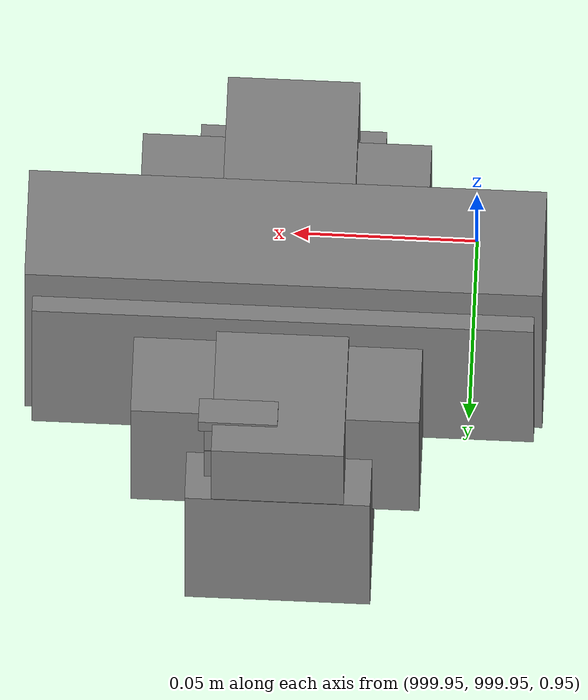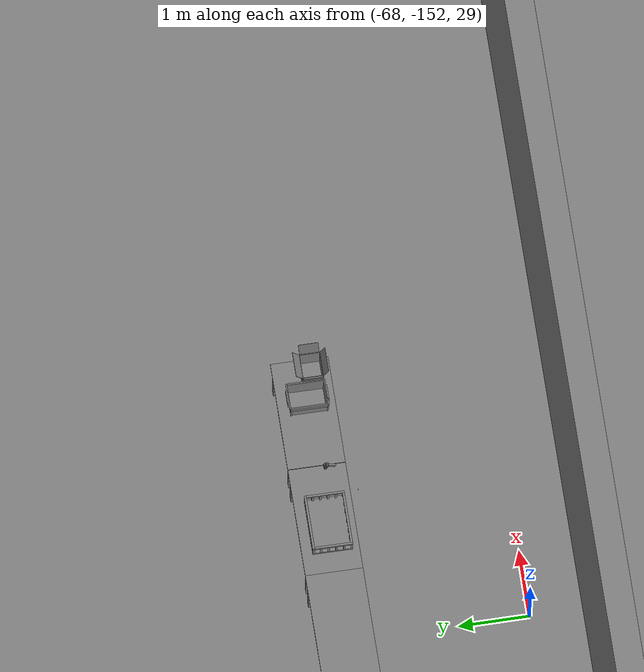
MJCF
<mujoco>
    <option gravity="0.000000000 0.000000000 -9.810000420" timestep="0.0049999999" integrator="implicitfast" density="1.225" viscosity="1.8000001e-05" noslip_iterations="10" iterations="100" sdf_iterations="50">
        <flag multiccd="disable"/>
    </option>
    <size memory="1000M"/>
    <compiler coordinate="local"/>
    <worldbody>
        <light cutoff="30" pos="0 1 1" dir="0 -1 -2"/>
        <light cutoff="30" pos="0 -1 1" dir="0 1 -2"/>
        <body pos="-64.866622925 -149.383972168 30.183746338" euler="89.999984741 89.999946594 0.000000000" name="openloong_gripper_2f85_fix_base_usda_bluebox_01">
            <geom contype="1" conaffinity="1" density="1000" type="box" material="" rgba="0.500000000 0.500000000 0.500000000 1.000000000" solimp="0.899999976 0.949999988 0.001000000" friction="1.000000000 0.005000000 0.000100000" solref="0.020000000 1.000000000" margin="0" condim="3" group="0" pos="0.276580811 0.187225342 0.000068665" quat="0.707106948 0.000077471 0.707106352 0.000077486" size="0.100000001 0.057999998 0.010000000" name="openloong_gripper_2f85_fix_base_usda_geom_7A749BBB_E923_4D53_86E7_BEB6B03D016F"/>
            <geom contype="1" conaffinity="1" density="1000" type="box" material="" rgba="0.500000000 0.500000000 0.500000000 1.000000000" solimp="0.899999976 0.949999988 0.001000000" friction="1.000000000 0.005000000 0.000100000" solref="0.020000000 1.000000000" margin="0" condim="3" group="0" pos="0.000000000 0.002883911 0.000000000" quat="0.999999881 0.000000000 0.000000000 0.000000000" size="0.254000008 0.003000000 0.172000006" name="openloong_gripper_2f85_fix_base_usda_geom_1E813ABF_2616_4204_B735_9A27E1B22D11"/>
            <geom contype="1" conaffinity="1" density="1000" type="box" material="" rgba="0.500000000 0.500000000 0.500000000 1.000000000" solimp="0.899999976 0.949999988 0.001000000" friction="1.000000000 0.005000000 0.000100000" solref="0.020000000 1.000000000" margin="0" condim="3" group="0" pos="0.000000000 0.124874115 0.173484802" quat="0.999796331 0.020176515 -0.000000015 0.000000030" size="0.259999990 0.119999997 0.007000000" name="openloong_gripper_2f85_fix_base_usda_geom_1FBAD682_0ED9_4F9A_B8AD_A05547005994"/>
            <geom contype="1" conaffinity="1" density="1000" type="box" material="" rgba="0.500000000 0.500000000 0.500000000 1.000000000" solimp="0.899999976 0.949999988 0.001000000" friction="1.000000000 0.005000000 0.000100000" solref="0.020000000 1.000000000" margin="0" condim="3" group="0" pos="0.000000000 0.124874115 -0.173469543" quat="0.999796331 -0.020176545 -0.000000015 0.000000000" size="0.259999990 0.119999997 0.007000000" name="openloong_gripper_2f85_fix_base_usda_geom_CACA29C6_5360_407F_91C3_518CC517384C"/>
            <geom contype="1" conaffinity="1" density="1000" type="box" material="" rgba="0.500000000 0.500000000 0.500000000 1.000000000" solimp="0.899999976 0.949999988 0.001000000" friction="1.000000000 0.005000000 0.000100000" solref="0.020000000 1.000000000" margin="0" condim="3" group="0" pos="0.000000000 0.214008331 0.188980103" quat="0.999912977 0.013176724 0.000000015 0.000000000" size="0.259999990 0.029999999 0.012500000" name="openloong_gripper_2f85_fix_base_usda_geom_487FE215_9F94_4B94_9CF7_D376AB38F94B"/>
            <geom contype="1" conaffinity="1" density="1000" type="box" material="" rgba="0.500000000 0.500000000 0.500000000 1.000000000" solimp="0.899999976 0.949999988 0.001000000" friction="1.000000000 0.005000000 0.000100000" solref="0.020000000 1.000000000" margin="0" condim="3" group="0" pos="-0.258361816 0.125289917 0.001876831" quat="0.702796936 -0.020792112 0.710783124 0.020769298" size="0.189999998 0.119999997 0.009000000" name="openloong_gripper_2f85_fix_base_usda_geom_304BF62F_68E4_4B5E_95AA_1294806AEEEF"/>
            <geom contype="1" conaffinity="1" density="1000" type="box" material="" rgba="0.500000000 0.500000000 0.500000000 1.000000000" solimp="0.899999976 0.949999988 0.001000000" friction="1.000000000 0.005000000 0.000100000" solref="0.020000000 1.000000000" margin="0" condim="3" group="0" pos="0.000000000 0.214008331 -0.188980103" quat="0.999912977 -0.013176769 0.000000030 0.000000015" size="0.259999990 0.029999999 0.012500000" name="openloong_gripper_2f85_fix_base_usda_geom_11DA4083_647D_4E0C_B61E_1E0FD9DB22EF"/>
            <geom contype="1" conaffinity="1" density="1000" type="box" material="" rgba="0.500000000 0.500000000 0.500000000 1.000000000" solimp="0.899999976 0.949999988 0.001000000" friction="1.000000000 0.005000000 0.000100000" solref="0.020000000 1.000000000" margin="0" condim="3" group="0" pos="-0.276611328 0.187225342 0.000068665" quat="0.707106650 0.000077441 0.707106709 0.000077456" size="0.100000001 0.057999998 0.010000000" name="openloong_gripper_2f85_fix_base_usda_geom_346D4AE7_654F_45E1_AF91_EE84CD9F3548"/>
            <geom contype="1" conaffinity="1" density="1000" type="box" material="" rgba="0.500000000 0.500000000 0.500000000 1.000000000" solimp="0.899999976 0.949999988 0.001000000" friction="1.000000000 0.005000000 0.000100000" solref="0.020000000 1.000000000" margin="0" condim="3" group="0" pos="0.258331299 0.125289917 0.001876831" quat="0.702851415 0.018856421 0.710823774 -0.019329369" size="0.189999998 0.119999997 0.009000000" name="openloong_gripper_2f85_fix_base_usda_geom_F53F65B9_5635_464E_9CE9_2450CF927EA0"/>
            <freejoint name="openloong_gripper_2f85_fix_base_usda_bluebox_01_joint"/>
            <site size="0.005000000 0.005000000 0.005000000" rgba="0.500000000 0.500000000 0.500000000 1.000000000" pos="0.000000000 0.000000000 0.000000000" quat="0.999961913 0.008726534 0.000000000 0.000000000" group="0" type="sphere" name="openloong_gripper_2f85_fix_base_usda_bluebox_01site"/>
        </body>
        <body pos="-64.496299744 -149.491867065 30.235729218" euler="0.000000000 0.000000000 89.999946594" name="openloong_gripper_2f85_fix_base_usda_cardboardbox_01">
            <geom contype="1" conaffinity="1" density="1000" type="box" material="" rgba="0.500000000 0.500000000 0.500000000 1.000000000" solimp="0.899999976 0.949999988 0.001000000" friction="1.000000000 0.005000000 0.000100000" solref="0.020000000 1.000000000" margin="0" condim="3" group="0" pos="-0.003166199 -0.004086494 0.005052090" quat="1.000000000 0.000000000 0.000000000 0.000000000" size="0.142499998 0.177500010 0.005000000" name="openloong_gripper_2f85_fix_base_usda_geom_234303D1_C5AC_4DCD_9223_13BFFB5D80E7"/>
            <geom contype="1" conaffinity="1" density="1000" type="box" material="" rgba="0.500000000 0.500000000 0.500000000 1.000000000" solimp="0.899999976 0.949999988 0.001000000" friction="1.000000000 0.005000000 0.000100000" solref="0.020000000 1.000000000" margin="0" condim="3" group="0" pos="-0.003166199 0.170316696 0.150570869" quat="1.000000000 0.000000000 0.000000000 0.000000000" size="0.142499998 0.005000000 0.149999991" name="openloong_gripper_2f85_fix_base_usda_geom_B4DA5605_322A_49E6_98E9_A08B0845CF5C"/>
            <geom contype="1" conaffinity="1" density="1000" type="box" material="" rgba="0.500000000 0.500000000 0.500000000 1.000000000" solimp="0.899999976 0.949999988 0.001000000" friction="1.000000000 0.005000000 0.000100000" solref="0.020000000 1.000000000" margin="0" condim="3" group="0" pos="-0.147399902 -0.005307198 0.150570869" quat="1.000000000 0.000000000 0.000000000 0.000000000" size="0.005000000 0.177500010 0.149999991" name="openloong_gripper_2f85_fix_base_usda_geom_31AE4D90_BCB1_4131_8D9A_F1E175CEC181"/>
            <geom contype="1" conaffinity="1" density="1000" type="box" material="" rgba="0.500000000 0.500000000 0.500000000 1.000000000" solimp="0.899999976 0.949999988 0.001000000" friction="1.000000000 0.005000000 0.000100000" solref="0.020000000 1.000000000" margin="0" condim="3" group="0" pos="0.140275955 -0.005307198 0.150570869" quat="1.000000000 0.000000000 0.000000000 0.000000000" size="0.005000000 0.177500010 0.149999991" name="openloong_gripper_2f85_fix_base_usda_geom_7968C0AD_D7A1_4627_923F_FB707E22CCB9"/>
            <geom contype="1" conaffinity="1" density="1000" type="box" material="" rgba="0.500000000 0.500000000 0.500000000 1.000000000" solimp="0.899999976 0.949999988 0.001000000" friction="1.000000000 0.005000000 0.000100000" solref="0.020000000 1.000000000" margin="0" condim="3" group="0" pos="-0.003166199 -0.181550980 0.150570869" quat="1.000000000 0.000000000 0.000000000 0.000000000" size="0.142499998 0.005000000 0.149999991" name="openloong_gripper_2f85_fix_base_usda_geom_324137CE_6931_4E07_B7A7_23356AB2DA62"/>
            <freejoint name="openloong_gripper_2f85_fix_base_usda_cardboardbox_01_joint"/>
            <site size="0.005000000 0.005000000 0.005000000" rgba="0.500000000 0.500000000 0.500000000 1.000000000" pos="0.000000000 0.000000000 0.000000000" quat="0.999961913 0.008726535 0.000000000 0.000000000" group="0" type="sphere" name="openloong_gripper_2f85_fix_base_usda_site_44AADE6A_AD13_4581_9BB8_7B267BA15C31"/>
            <body pos="0.139160156 -0.004048347 0.301930904" euler="-179.999954224 49.383502960 179.999954224" name="openloong_gripper_2f85_fix_base_usda_A1_006">
                <geom contype="1" conaffinity="1" density="1000" type="box" material="" rgba="0.500000000 0.500000000 0.500000000 1.000000000" solimp="0.899999976 0.949999988 0.001000000" friction="1.000000000 0.005000000 0.000100000" solref="0.020000000 1.000000000" margin="0" condim="3" group="0" pos="-0.071587563 0.000009537 0.001745224" quat="0.999999881 0.000000000 0.000000000 0.000000000" size="0.071249999 0.179999992 0.002500000" name="openloong_gripper_2f85_fix_base_usda_geom_7BAE9D24_1746_4AE1_9907_0D099E20C58C"/>
                <joint armature="0" stiffness="0.07" damping="0.0099999998" axis="0.000000 1.000000 0.000000" type="hinge" name="openloong_gripper_2f85_fix_base_usda_A1_006"/>
            </body>
            <body pos="-0.145902634 -0.004086494 0.301938057" euler="-180.000000000 -60.000011444 -180.000000000" name="openloong_gripper_2f85_fix_base_usda_A2_006">
                <geom contype="1" conaffinity="1" density="1000" type="box" material="" rgba="0.500000000 0.500000000 0.500000000 1.000000000" solimp="0.899999976 0.949999988 0.001000000" friction="1.000000000 0.005000000 0.000100000" solref="0.020000000 1.000000000" margin="0" condim="3" group="0" pos="0.071268082 0.000009537 0.002717972" quat="0.000002921 0.000000000 -0.000000030 0.999999881" size="0.071249999 0.179999992 0.002500000" name="openloong_gripper_2f85_fix_base_usda_geom_CF332E00_8696_41A9_8490_87D4E673FB6F"/>
                <joint armature="0" stiffness="0.07" damping="0.0099999998" axis="0.000000 1.000000 0.000000" type="hinge" name="openloong_gripper_2f85_fix_base_usda_A2_006"/>
            </body>
            <body pos="-0.003385544 0.175991058 0.301930904" euler="-125.858116150 -0.000004561 0.000002331" name="openloong_gripper_2f85_fix_base_usda_B2_006">
                <geom contype="1" conaffinity="1" density="1000" type="box" material="" rgba="0.500000000 0.500000000 0.500000000 1.000000000" solimp="0.899999976 0.949999988 0.001000000" friction="1.000000000 0.005000000 0.000100000" solref="0.020000000 1.000000000" margin="0" condim="3" group="0" pos="0.000009537 -0.070939064 -0.002470016" quat="0.999614120 0.027776197 -0.000000015 0.000000030" size="0.137500003 0.064999998 0.005000000" name="openloong_gripper_2f85_fix_base_usda_geom_E40BCE5B_5F05_4108_BD34_72E36842E603"/>
                <joint armature="0" stiffness="0.07" damping="0.0099999998" axis="1.000000 0.000000 0.000000" type="hinge" name="openloong_gripper_2f85_fix_base_usda_B2_006"/>
            </body>
            <body pos="-0.003385544 -0.184140205 0.301938057" euler="147.805557251 0.000000000 0.000000000" name="openloong_gripper_2f85_fix_base_usda_B1_006">
                <geom contype="1" conaffinity="1" density="1000" type="box" material="" rgba="0.500000000 0.500000000 0.500000000 1.000000000" solimp="0.899999976 0.949999988 0.001000000" friction="1.000000000 0.005000000 0.000100000" solref="0.020000000 1.000000000" margin="0" condim="3" group="0" pos="-0.000028610 0.070202351 -0.002703667" quat="0.999614179 -0.027776167 0.000000000 0.000000000" size="0.137500003 0.064999998 0.005000000" name="openloong_gripper_2f85_fix_base_usda_geom_31AF0335_8EB6_439D_8CCB_CA5F3F2F17E8"/>
                <joint armature="0" stiffness="0.07" damping="0.0099999998" axis="1.000000 0.000000 0.000000" type="hinge" name="openloong_gripper_2f85_fix_base_usda_B1_006"/>
            </body>
        </body>
        <body pos="-65.882858276 -149.481979370 30.229999542" euler="-64.487716675 0.000000000 0.000000000" name="openloong_gripper_2f85_fix_base_usda_Barcode">
            <geom contype="1" conaffinity="1" density="1000" type="box" material="" rgba="0.500000000 0.500000000 0.500000000 1.000000000" solimp="0.899999976 0.949999988 0.001000000" friction="1.000000000 0.005000000 0.000100000" solref="0.020000000 1.000000000" margin="0" condim="3" group="0" pos="0.000000000 0.013038635 0.001419067" quat="0.000000000 0.000000000 0.000000000 1.000000119" size="0.034000002 0.010000000 0.017999999" name="openloong_gripper_2f85_fix_base_usda_geom_993EA998_C94D_42DE_A107_469764DF9B83"/>
            <geom contype="1" conaffinity="1" density="1000" type="box" material="" rgba="0.500000000 0.500000000 0.500000000 1.000000000" solimp="0.899999976 0.949999988 0.001000000" friction="1.000000000 0.005000000 0.000100000" solref="0.020000000 1.000000000" margin="0" condim="3" group="0" pos="0.000000000 -0.035301208 -0.007095337" quat="0.000000000 0.000000000 -0.043619365 0.999048233" size="0.028999999 0.010000000 0.020000000" name="openloong_gripper_2f85_fix_base_usda_geom_ED375B59_500E_4625_B421_D135455F0A89"/>
            <geom contype="1" conaffinity="1" density="1000" type="box" material="" rgba="0.500000000 0.500000000 0.500000000 1.000000000" solimp="0.899999976 0.949999988 0.001000000" friction="1.000000000 0.005000000 0.000100000" solref="0.020000000 1.000000000" margin="0" condim="3" group="0" pos="0.000000000 -0.043411255 -0.011749268" quat="0.922262907 0.386563420 0.000000000 0.000000000" size="0.026000001 0.010000000 0.020000000" name="openloong_gripper_2f85_fix_base_usda_geom_37F6A408_D97B_4432_BD5E_2D3EC138B69C"/>
            <geom contype="1" conaffinity="1" density="1000" type="box" material="" rgba="0.500000000 0.500000000 0.500000000 1.000000000" solimp="0.899999976 0.949999988 0.001000000" friction="1.000000000 0.005000000 0.000100000" solref="0.020000000 1.000000000" margin="0" condim="3" group="0" pos="0.000000000 -0.016967773 -0.031860352" quat="0.000000000 0.000000000 0.000000000 1.000000119" size="0.008000000 0.010000000 0.013000000" name="openloong_gripper_2f85_fix_base_usda_geom_172FF999_5F41_491D_9759_4CCC410B90CA"/>
            <geom contype="1" conaffinity="1" density="1000" type="box" material="" rgba="0.500000000 0.500000000 0.500000000 1.000000000" solimp="0.899999976 0.949999988 0.001000000" friction="1.000000000 0.005000000 0.000100000" solref="0.020000000 1.000000000" margin="0" condim="3" group="0" pos="0.000000000 -0.001869202 0.000312805" quat="0.953716993 0.300705761 0.000000000 0.000000000" size="0.032000002 0.010000000 0.018999999" name="openloong_gripper_2f85_fix_base_usda_geom_2CBC1B94_9B20_44D5_93D6_7C96C365C7E9"/>
            <geom contype="1" conaffinity="1" density="1000" type="box" material="" rgba="0.500000000 0.500000000 0.500000000 1.000000000" solimp="0.899999976 0.949999988 0.001000000" friction="1.000000000 0.005000000 0.000100000" solref="0.020000000 1.000000000" margin="0" condim="3" group="0" pos="0.000000000 -0.019531250 -0.003173828" quat="0.953716993 0.300705761 0.000000000 0.000000000" size="0.030999999 0.010000000 0.020000000" name="openloong_gripper_2f85_fix_base_usda_geom_D1F8E5C0_54FC_4D95_B69D_C2E766C04520"/>
            <geom contype="1" conaffinity="1" density="1000" type="box" material="" rgba="0.500000000 0.500000000 0.500000000 1.000000000" solimp="0.899999976 0.949999988 0.001000000" friction="1.000000000 0.005000000 0.000100000" solref="0.020000000 1.000000000" margin="0" condim="3" group="0" pos="0.000000000 -0.035301208 -0.007095337" quat="0.953716993 0.300705761 0.000000000 0.000000000" size="0.028999999 0.010000000 0.020000000" name="openloong_gripper_2f85_fix_base_usda_geom_B8C5036B_0330_4402_88FF_5DDCE699F917"/>
            <geom contype="1" conaffinity="1" density="1000" type="box" material="" rgba="0.500000000 0.500000000 0.500000000 1.000000000" solimp="0.899999976 0.949999988 0.001000000" friction="1.000000000 0.005000000 0.000100000" solref="0.020000000 1.000000000" margin="0" condim="3" group="0" pos="0.000000000 -0.042617798 -0.071121216" quat="0.000000000 0.000000000 0.000000000 1.000000119" size="0.013000000 0.021000000 0.059999999" name="openloong_gripper_2f85_fix_base_usda_geom_A56DA052_DD90_4726_84BC_0CDC6CDB61EB"/>
            <freejoint name="openloong_gripper_2f85_fix_base_usda_Barcode_joint"/>
            <site size="0.005000000 0.005000000 0.005000000" rgba="0.500000000 0.500000000 0.500000000 1.000000000" pos="0.000000000 0.000000000 0.000000000" quat="1.000000000 0.000000000 0.000000000 0.000000000" group="0" type="sphere" name="openloong_gripper_2f85_fix_base_usda_Barcode_site"/>
        </body>
        <body pos="-66.745018005 -149.392349243 30.184000015" euler="0.000000000 0.000000000 89.999946594" name="[22333128775688]_Basket_01">
            <geom contype="1" conaffinity="1" density="1000" type="box" material="" rgba="0.500000000 0.500000000 0.500000000 1.000000000" solimp="0.899999976 0.949999988 0.001000000" friction="1.000000000 0.005000000 0.000100000" solref="0.020000000 1.000000000" margin="0" condim="3" group="0" pos="-0.052425385 0.389207840 0.089787483" quat="0.707107008 0.000000000 0.000000000 0.707106411" size="0.014249999 0.014249999 0.059999999" name="[22333128775688]_geom_ABD278F7_FDBA_4307_A7AC_6458D053FCEC"/>
            <geom contype="1" conaffinity="1" density="1000" type="box" material="" rgba="0.500000000 0.500000000 0.500000000 1.000000000" solimp="0.899999976 0.949999988 0.001000000" friction="1.000000000 0.005000000 0.000100000" solref="0.020000000 1.000000000" margin="0" condim="3" group="0" pos="0.264015198 -0.133043289 0.089787483" quat="0.707107008 0.000000000 0.000000000 0.707106411" size="0.014249999 0.014249999 0.059999999" name="[22333128775688]_geom_3BE6A8BC_A06D_43F3_9C83_071BAC36D952"/>
            <geom contype="1" conaffinity="1" density="1000" type="box" material="" rgba="0.500000000 0.500000000 0.500000000 1.000000000" solimp="0.899999976 0.949999988 0.001000000" friction="1.000000000 0.005000000 0.000100000" solref="0.020000000 1.000000000" margin="0" condim="3" group="0" pos="-0.264015198 -0.265548706 0.089793205" quat="0.707107008 0.000000000 0.000000000 0.707106411" size="0.014249999 0.014249999 0.059999999" name="[22333128775688]_geom_2AF5BBF6_94AF_4F7A_A79A_1C8243B57046"/>
            <geom contype="1" conaffinity="1" density="1000" type="box" material="" rgba="0.500000000 0.500000000 0.500000000 1.000000000" solimp="0.899999976 0.949999988 0.001000000" friction="1.000000000 0.005000000 0.000100000" solref="0.020000000 1.000000000" margin="0" condim="3" group="0" pos="-0.160263062 -0.389322281 0.089793205" quat="0.707107008 0.000000000 0.000000000 0.707106411" size="0.014249999 0.014249999 0.059999999" name="[22333128775688]_geom_7588ECA9_C9D7_4724_9014_920D7354EEFC"/>
            <geom contype="1" conaffinity="1" density="1000" type="box" material="" rgba="0.500000000 0.500000000 0.500000000 1.000000000" solimp="0.899999976 0.949999988 0.001000000" friction="1.000000000 0.005000000 0.000100000" solref="0.020000000 1.000000000" margin="0" condim="3" group="0" pos="0.162265778 -0.389322281 0.089787483" quat="0.707107008 0.000000000 0.000000000 0.707106411" size="0.014249999 0.014249999 0.059999999" name="[22333128775688]_geom_282E825F_67FB_4427_BC12_63CF86D07544"/>
            <geom contype="1" conaffinity="1" density="1000" type="box" material="" rgba="0.500000000 0.500000000 0.500000000 1.000000000" solimp="0.899999976 0.949999988 0.001000000" friction="1.000000000 0.005000000 0.000100000" solref="0.020000000 1.000000000" margin="0" condim="3" group="0" pos="0.264015198 0.389207840 0.089787483" quat="0.707107008 0.000000000 0.000000000 0.707106411" size="0.014249999 0.014249999 0.059999999" name="[22333128775688]_geom_6B58C677_2B99_4328_87DF_3498CE827D40"/>
            <geom contype="1" conaffinity="1" density="1000" type="box" material="" rgba="0.500000000 0.500000000 0.500000000 1.000000000" solimp="0.899999976 0.949999988 0.001000000" friction="1.000000000 0.005000000 0.000100000" solref="0.020000000 1.000000000" margin="0" condim="3" group="0" pos="-0.264015198 -0.133043289 0.089793205" quat="0.707107008 0.000000000 0.000000000 0.707106411" size="0.014249999 0.014249999 0.059999999" name="[22333128775688]_geom_1BBDE88C_EE0F_43D9_B6D4_939EC1257F0C"/>
            <geom contype="1" conaffinity="1" density="1000" type="box" material="" rgba="0.500000000 0.500000000 0.500000000 1.000000000" solimp="0.899999976 0.949999988 0.001000000" friction="1.000000000 0.005000000 0.000100000" solref="0.020000000 1.000000000" margin="0" condim="3" group="0" pos="-0.264026642 0.269256592 0.089793205" quat="0.707107008 0.000000000 0.000000000 0.707106411" size="0.014249999 0.014249999 0.059999999" name="[22333128775688]_geom_92F5EEAC_A468_4FCD_B85B_8954E27B102F"/>
            <geom contype="1" conaffinity="1" density="1000" type="box" material="" rgba="0.500000000 0.500000000 0.500000000 1.000000000" solimp="0.899999976 0.949999988 0.001000000" friction="1.000000000 0.005000000 0.000100000" solref="0.020000000 1.000000000" margin="0" condim="3" group="0" pos="0.054462433 0.389207840 0.089787483" quat="0.707107008 0.000000000 0.000000000 0.707106411" size="0.014249999 0.014249999 0.059999999" name="[22333128775688]_geom_56FAD1D0_B5A5_4FA9_A40D_B753010F636B"/>
            <geom contype="1" conaffinity="1" density="1000" type="box" material="" rgba="0.500000000 0.500000000 0.500000000 1.000000000" solimp="0.899999976 0.949999988 0.001000000" friction="1.000000000 0.005000000 0.000100000" solref="0.020000000 1.000000000" margin="0" condim="3" group="0" pos="0.054462433 -0.389322281 0.089787483" quat="0.707107008 0.000000000 0.000000000 0.707106411" size="0.014249999 0.014249999 0.059999999" name="[22333128775688]_geom_AA2448F0_7FD5_4F6B_8653_62FDC2F06A18"/>
            <geom contype="1" conaffinity="1" density="1000" type="box" material="" rgba="0.500000000 0.500000000 0.500000000 1.000000000" solimp="0.899999976 0.949999988 0.001000000" friction="1.000000000 0.005000000 0.000100000" solref="0.020000000 1.000000000" margin="0" condim="3" group="0" pos="0.264015198 0.269256592 0.089793205" quat="0.707107008 0.000000000 0.000000000 0.707106411" size="0.014249999 0.014249999 0.059999999" name="[22333128775688]_geom_878A18F2_25E6_4C8D_8082_AF2DD26CB6A0"/>
            <geom contype="1" conaffinity="1" density="1000" type="box" material="" rgba="0.500000000 0.500000000 0.500000000 1.000000000" solimp="0.899999976 0.949999988 0.001000000" friction="1.000000000 0.005000000 0.000100000" solref="0.020000000 1.000000000" margin="0" condim="3" group="0" pos="0.264015198 -0.389322281 0.089787483" quat="0.707107008 0.000000000 0.000000000 0.707106411" size="0.014249999 0.014249999 0.059999999" name="[22333128775688]_geom_1F9CF7D6_A1B4_4845_96CC_B4E4D340088B"/>
            <geom contype="1" conaffinity="1" density="1000" type="box" material="" rgba="0.500000000 0.500000000 0.500000000 1.000000000" solimp="0.899999976 0.949999988 0.001000000" friction="1.000000000 0.005000000 0.000100000" solref="0.020000000 1.000000000" margin="0" condim="3" group="0" pos="0.000000000 0.000000000 0.015998840" quat="0.707107008 0.000000000 0.000000000 0.707106411" size="0.403499991 0.279000014 0.015750000" name="[22333128775688]_geom_05657DC1_CC94_49DA_A8D3_0CFC7C80BDEA"/>
            <geom contype="1" conaffinity="1" density="1000" type="box" material="" rgba="0.500000000 0.500000000 0.500000000 1.000000000" solimp="0.899999976 0.949999988 0.001000000" friction="1.000000000 0.005000000 0.000100000" solref="0.020000000 1.000000000" margin="0" condim="3" group="0" pos="0.000000000 -0.389476776 0.163619041" quat="0.707107008 0.000000000 0.000000000 0.707106411" size="0.015000000 0.277500004 0.015750000" name="[22333128775688]_geom_1DAF29BA_2579_4AD5_90FC_EE8DCE6A388E"/>
            <geom contype="1" conaffinity="1" density="1000" type="box" material="" rgba="0.500000000 0.500000000 0.500000000 1.000000000" solimp="0.899999976 0.949999988 0.001000000" friction="1.000000000 0.005000000 0.000100000" solref="0.020000000 1.000000000" margin="0" condim="3" group="0" pos="0.162265778 0.389207840 0.089787483" quat="0.707107008 0.000000000 0.000000000 0.707106411" size="0.014249999 0.014249999 0.059999999" name="[22333128775688]_geom_9B4C4899_0AB9_4AE0_97C1_47BE4F237F1A"/>
            <geom contype="1" conaffinity="1" density="1000" type="box" material="" rgba="0.500000000 0.500000000 0.500000000 1.000000000" solimp="0.899999976 0.949999988 0.001000000" friction="1.000000000 0.005000000 0.000100000" solref="0.020000000 1.000000000" margin="0" condim="3" group="0" pos="0.000000000 0.389471054 0.163619041" quat="0.707107008 0.000000000 0.000000000 0.707106411" size="0.015000000 0.277500004 0.015750000" name="[22333128775688]_geom_19C12ECF_47D5_4E11_B395_7AFCDEDB115D"/>
            <geom contype="1" conaffinity="1" density="1000" type="box" material="" rgba="0.500000000 0.500000000 0.500000000 1.000000000" solimp="0.899999976 0.949999988 0.001000000" friction="1.000000000 0.005000000 0.000100000" solref="0.020000000 1.000000000" margin="0" condim="3" group="0" pos="-0.263511658 0.000000000 0.163619041" quat="0.707107008 0.000000000 0.000000000 0.707106411" size="0.403499991 0.015000000 0.015750000" name="[22333128775688]_geom_5E2A1DDB_9242_41C8_B8DE_C20E406FD017"/>
            <geom contype="1" conaffinity="1" density="1000" type="box" material="" rgba="0.500000000 0.500000000 0.500000000 1.000000000" solimp="0.899999976 0.949999988 0.001000000" friction="1.000000000 0.005000000 0.000100000" solref="0.020000000 1.000000000" margin="0" condim="3" group="0" pos="-0.264015198 0.141334534 0.089793205" quat="0.707107008 0.000000000 0.000000000 0.707106411" size="0.014249999 0.014249999 0.059999999" name="[22333128775688]_geom_486C256B_ED54_47A9_A510_1FC45008F168"/>
            <geom contype="1" conaffinity="1" density="1000" type="box" material="" rgba="0.500000000 0.500000000 0.500000000 1.000000000" solimp="0.899999976 0.949999988 0.001000000" friction="1.000000000 0.005000000 0.000100000" solref="0.020000000 1.000000000" margin="0" condim="3" group="0" pos="0.264015198 -0.265548706 0.089787483" quat="0.707107008 0.000000000 0.000000000 0.707106411" size="0.014249999 0.014249999 0.059999999" name="[22333128775688]_geom_AD235D89_F994_4611_8482_DC51EB33F0B8"/>
            <geom contype="1" conaffinity="1" density="1000" type="box" material="" rgba="0.500000000 0.500000000 0.500000000 1.000000000" solimp="0.899999976 0.949999988 0.001000000" friction="1.000000000 0.005000000 0.000100000" solref="0.020000000 1.000000000" margin="0" condim="3" group="0" pos="-0.160263062 0.389207840 0.089787483" quat="0.707107008 0.000000000 0.000000000 0.707106411" size="0.014249999 0.014249999 0.059999999" name="[22333128775688]_geom_3F443074_C641_431D_85B5_4788E56C7281"/>
            <geom contype="1" conaffinity="1" density="1000" type="box" material="" rgba="0.500000000 0.500000000 0.500000000 1.000000000" solimp="0.899999976 0.949999988 0.001000000" friction="1.000000000 0.005000000 0.000100000" solref="0.020000000 1.000000000" margin="0" condim="3" group="0" pos="-0.052425385 -0.389322281 0.089787483" quat="0.707107008 0.000000000 0.000000000 0.707106411" size="0.014249999 0.014249999 0.059999999" name="[22333128775688]_geom_E6AEC45E_A13E_4E1D_A11E_B4A378385609"/>
            <geom contype="1" conaffinity="1" density="1000" type="box" material="" rgba="0.500000000 0.500000000 0.500000000 1.000000000" solimp="0.899999976 0.949999988 0.001000000" friction="1.000000000 0.005000000 0.000100000" solref="0.020000000 1.000000000" margin="0" condim="3" group="0" pos="-0.264026642 -0.389322281 0.089793205" quat="0.707107008 0.000000000 0.000000000 0.707106411" size="0.014249999 0.014249999 0.059999999" name="[22333128775688]_geom_833E18D3_5BBF_4334_AD99_2AF100CC1A6B"/>
            <geom contype="1" conaffinity="1" density="1000" type="box" material="" rgba="0.500000000 0.500000000 0.500000000 1.000000000" solimp="0.899999976 0.949999988 0.001000000" friction="1.000000000 0.005000000 0.000100000" solref="0.020000000 1.000000000" margin="0" condim="3" group="0" pos="0.264015198 0.141334534 0.089787483" quat="0.707107008 0.000000000 0.000000000 0.707106411" size="0.014249999 0.014249999 0.059999999" name="[22333128775688]_geom_C911250F_61FE_46A2_9CF7_576AA614F325"/>
            <geom contype="1" conaffinity="1" density="1000" type="box" material="" rgba="0.500000000 0.500000000 0.500000000 1.000000000" solimp="0.899999976 0.949999988 0.001000000" friction="1.000000000 0.005000000 0.000100000" solref="0.020000000 1.000000000" margin="0" condim="3" group="0" pos="-0.264015198 0.389207840 0.089793205" quat="0.707107008 0.000000000 0.000000000 0.707106411" size="0.014249999 0.014249999 0.059999999" name="[22333128775688]_geom_AFAD3E6E_CD78_4DB3_8C73_58D489260882"/>
            <geom contype="1" conaffinity="1" density="1000" type="box" material="" rgba="0.500000000 0.500000000 0.500000000 1.000000000" solimp="0.899999976 0.949999988 0.001000000" friction="1.000000000 0.005000000 0.000100000" solref="0.020000000 1.000000000" margin="0" condim="3" group="0" pos="0.264015198 0.004480362 0.089787483" quat="0.707107008 0.000000000 0.000000000 0.707106411" size="0.014249999 0.014249999 0.059999999" name="[22333128775688]_geom_D9ECD87D_56B7_4ADE_9B7A_246F211A895F"/>
            <geom contype="1" conaffinity="1" density="1000" type="box" material="" rgba="0.500000000 0.500000000 0.500000000 1.000000000" solimp="0.899999976 0.949999988 0.001000000" friction="1.000000000 0.005000000 0.000100000" solref="0.020000000 1.000000000" margin="0" condim="3" group="0" pos="0.263694763 -0.000011444 0.163619041" quat="0.707107008 0.000000000 0.000000000 0.707106411" size="0.403499991 0.015000000 0.015750000" name="[22333128775688]_geom_A72E8A79_F535_4584_AC71_93CCBF0B687B"/>
            <geom contype="1" conaffinity="1" density="1000" type="box" material="" rgba="0.500000000 0.500000000 0.500000000 1.000000000" solimp="0.899999976 0.949999988 0.001000000" friction="1.000000000 0.005000000 0.000100000" solref="0.020000000 1.000000000" margin="0" condim="3" group="0" pos="-0.264015198 0.004480362 0.089793205" quat="0.707107008 0.000000000 0.000000000 0.707106411" size="0.014249999 0.014249999 0.059999999" name="[22333128775688]_geom_E2F885B4_1E1F_42BB_A589_2899128BEDF2"/>
            <freejoint name="[22333128775688]_joint_817830C3_1D6F_419F_B956_1732EA6C586D"/>
        </body>
        <body pos="0.000000000 0.000000000 0.000000000" euler="0.000000000 0.000000000 0.000000000" name="Static Objects_Static Objects">
            <geom contype="1" conaffinity="1" density="1000" type="box" material="" rgba="0.500000000 0.500000000 0.500000000 1.000000000" solimp="0.899999976 0.949999988 0.001000000" friction="1.000000000 0.005000000 0.000100000" solref="0.020000000 1.000000000" margin="0" condim="3" group="0" pos="-67.544113159 -149.365814209 29.727830887" quat="0.500000417 0.499999970 0.499999553 0.499999970" size="0.381000012 0.319999993 0.041000001" name="Static Objects_geom_6A8EA926_E91F_48F9_B7F8_C9FE034AA9B7"/>
            <geom contype="1" conaffinity="1" density="1000" type="box" material="" rgba="0.500000000 0.500000000 0.500000000 1.000000000" solimp="0.899999976 0.949999988 0.001000000" friction="1.000000000 0.005000000 0.000100000" solref="0.020000000 1.000000000" margin="0" condim="3" group="0" pos="-68.239501953 -149.365814209 30.086868286" quat="0.500000417 0.499999970 0.499999553 0.499999970" size="0.370999992 0.039500002 0.745000005" name="Static Objects_geom_46670D1D_919B_497B_AD25_F5DFCC2374AA"/>
            <geom contype="1" conaffinity="1" density="1000" type="box" material="" rgba="0.500000000 0.500000000 0.500000000 1.000000000" solimp="0.899999976 0.949999988 0.001000000" friction="1.000000000 0.005000000 0.000100000" solref="0.020000000 1.000000000" margin="0" condim="3" group="0" pos="-68.239501953 -149.365814209 30.147235870" quat="0.500000417 0.499999970 0.499999553 0.499999970" size="0.400000006 0.022000000 0.800000012" name="Static Objects_geom_A6E007A4_F805_4924_ABA0_1E0CAD740E90"/>
            <geom contype="1" conaffinity="1" density="1000" type="box" material="" rgba="0.500000000 0.500000000 0.500000000 1.000000000" solimp="0.899999976 0.949999988 0.001000000" friction="1.000000000 0.005000000 0.000100000" solref="0.020000000 1.000000000" margin="0" condim="3" group="0" pos="-68.934890747 -149.365814209 29.727830887" quat="0.500000417 0.499999970 0.499999553 0.499999970" size="0.381000012 0.319999993 0.041000001" name="Static Objects_geom_3F600DBC_65F2_49B6_B20D_7248072990FD"/>
            <geom contype="1" conaffinity="1" density="1000" type="box" material="" rgba="0.500000000 0.500000000 0.500000000 1.000000000" solimp="0.899999976 0.949999988 0.001000000" friction="1.000000000 0.005000000 0.000100000" solref="0.020000000 1.000000000" margin="0" condim="3" group="0" pos="-68.239501953 -149.365814209 29.561563492" quat="0.500000417 0.499999970 0.499999553 0.499999970" size="0.020000000 0.022000000 0.660000026" name="Static Objects_geom_680AF058_24F4_4D72_AE49_F2C9AA949CB2"/>
            <geom contype="1" conaffinity="1" density="1000" type="box" material="" rgba="0.500000000 0.500000000 0.500000000 1.000000000" solimp="0.899999976 0.949999988 0.001000000" friction="1.000000000 0.005000000 0.000100000" solref="0.020000000 1.000000000" margin="0" condim="3" group="0" pos="-65.945671082 -149.365814209 29.727830887" quat="0.500000417 0.499999970 0.499999553 0.499999970" size="0.381000012 0.319999993 0.041000001" name="Static Objects_geom_22228C0A_000F_4610_82B3_47A0798F3BD9"/>
            <geom contype="1" conaffinity="1" density="1000" type="box" material="" rgba="0.500000000 0.500000000 0.500000000 1.000000000" solimp="0.899999976 0.949999988 0.001000000" friction="1.000000000 0.005000000 0.000100000" solref="0.020000000 1.000000000" margin="0" condim="3" group="0" pos="-66.641059875 -149.365814209 30.086868286" quat="0.500000417 0.499999970 0.499999553 0.499999970" size="0.370999992 0.039500002 0.745000005" name="Static Objects_geom_E3775A7D_11B4_4D90_929B_B17511A9295D"/>
            <geom contype="1" conaffinity="1" density="1000" type="box" material="" rgba="0.500000000 0.500000000 0.500000000 1.000000000" solimp="0.899999976 0.949999988 0.001000000" friction="1.000000000 0.005000000 0.000100000" solref="0.020000000 1.000000000" margin="0" condim="3" group="0" pos="-66.641059875 -149.365814209 30.147235870" quat="0.500000417 0.499999970 0.499999553 0.499999970" size="0.400000006 0.022000000 0.800000012" name="Static Objects_geom_8B46EE0E_22BF_4877_B34A_C6B81FB1D1C4"/>
            <geom contype="1" conaffinity="1" density="1000" type="box" material="" rgba="0.500000000 0.500000000 0.500000000 1.000000000" solimp="0.899999976 0.949999988 0.001000000" friction="1.000000000 0.005000000 0.000100000" solref="0.020000000 1.000000000" margin="0" condim="3" group="0" pos="-67.336448669 -149.365814209 29.727830887" quat="0.500000417 0.499999970 0.499999553 0.499999970" size="0.381000012 0.319999993 0.041000001" name="Static Objects_geom_D538F9B5_2D61_47E7_9947_1F618916985F"/>
            <geom contype="1" conaffinity="1" density="1000" type="box" material="" rgba="0.500000000 0.500000000 0.500000000 1.000000000" solimp="0.899999976 0.949999988 0.001000000" friction="1.000000000 0.005000000 0.000100000" solref="0.020000000 1.000000000" margin="0" condim="3" group="0" pos="-66.641059875 -149.365814209 29.561563492" quat="0.500000417 0.499999970 0.499999553 0.499999970" size="0.020000000 0.022000000 0.660000026" name="Static Objects_geom_04B01ED6_49F2_4B15_9775_9FAE766591E3"/>
            <geom contype="1" conaffinity="1" density="1000" type="box" material="" rgba="0.500000000 0.500000000 0.500000000 1.000000000" solimp="0.899999976 0.949999988 0.001000000" friction="1.000000000 0.005000000 0.000100000" solref="0.020000000 1.000000000" margin="0" condim="3" group="0" pos="-64.338577271 -149.365814209 29.727830887" quat="0.500000417 0.499999970 0.499999553 0.499999970" size="0.381000012 0.319999993 0.041000001" name="Static Objects_geom_187D6A9F_A951_4644_95C3_A999F9BCC2CA"/>
            <geom contype="1" conaffinity="1" density="1000" type="box" material="" rgba="0.500000000 0.500000000 0.500000000 1.000000000" solimp="0.899999976 0.949999988 0.001000000" friction="1.000000000 0.005000000 0.000100000" solref="0.020000000 1.000000000" margin="0" condim="3" group="0" pos="-65.033966064 -149.365814209 30.086868286" quat="0.500000417 0.499999970 0.499999553 0.499999970" size="0.370999992 0.039500002 0.745000005" name="Static Objects_geom_F071D3C6_DFFB_4F1B_8E43_6DAD17682A55"/>
            <geom contype="1" conaffinity="1" density="1000" type="box" material="" rgba="0.500000000 0.500000000 0.500000000 1.000000000" solimp="0.899999976 0.949999988 0.001000000" friction="1.000000000 0.005000000 0.000100000" solref="0.020000000 1.000000000" margin="0" condim="3" group="0" pos="-65.033966064 -149.365814209 30.147235870" quat="0.500000417 0.499999970 0.499999553 0.499999970" size="0.400000006 0.022000000 0.800000012" name="Static Objects_geom_1433183D_E0EE_4109_B1F2_16E5CCD740EA"/>
            <geom contype="1" conaffinity="1" density="1000" type="box" material="" rgba="0.500000000 0.500000000 0.500000000 1.000000000" solimp="0.899999976 0.949999988 0.001000000" friction="1.000000000 0.005000000 0.000100000" solref="0.020000000 1.000000000" margin="0" condim="3" group="0" pos="-65.729354858 -149.365814209 29.727830887" quat="0.500000417 0.499999970 0.499999553 0.499999970" size="0.381000012 0.319999993 0.041000001" name="Static Objects_geom_EA87CC15_57E0_4C3B_A737_EFEA828AE798"/>
            <geom contype="1" conaffinity="1" density="1000" type="box" material="" rgba="0.500000000 0.500000000 0.500000000 1.000000000" solimp="0.899999976 0.949999988 0.001000000" friction="1.000000000 0.005000000 0.000100000" solref="0.020000000 1.000000000" margin="0" condim="3" group="0" pos="-65.033966064 -149.365814209 29.561563492" quat="0.500000417 0.499999970 0.499999553 0.499999970" size="0.020000000 0.022000000 0.660000026" name="Static Objects_geom_E33E49C7_E98D_4E4A_9933_DE64BCB753E8"/>
            <geom contype="1" conaffinity="1" density="1000" type="box" material="" rgba="0.500000000 0.500000000 0.500000000 1.000000000" solimp="0.899999976 0.949999988 0.001000000" friction="1.000000000 0.005000000 0.000100000" solref="0.020000000 1.000000000" margin="0" condim="3" group="0" pos="-61.754566193 -137.853729248 33.906845093" quat="0.707107067 0.000000000 0.000000000 0.707106471" size="0.759999990 0.759999990 4.500000000" name="Static Objects_geom_7E7288A3_1E48_416E_96A8_3BB755A527A1"/>
            <geom contype="1" conaffinity="1" density="1000" type="box" material="" rgba="0.500000000 0.500000000 0.500000000 1.000000000" solimp="0.899999976 0.949999988 0.001000000" friction="1.000000000 0.005000000 0.000100000" solref="0.020000000 1.000000000" margin="0" condim="3" group="0" pos="-57.511135101 -144.927108765 31.707921982" quat="1.000000000 0.000000000 0.000000000 0.000000000" size="0.200000003 8.000000000 2.299999952" name="Static Objects_geom_DCCAE429_1EE2_48E3_BFB9_C9FA20DEFCA7"/>
            <geom contype="1" conaffinity="1" density="1000" type="box" material="" rgba="0.500000000 0.500000000 0.500000000 1.000000000" solimp="0.899999976 0.949999988 0.001000000" friction="1.000000000 0.005000000 0.000100000" solref="0.020000000 1.000000000" margin="0" condim="3" group="0" pos="-80.517646790 -157.574050903 31.688196182" quat="0.707107067 0.000000000 0.000000000 0.707106471" size="0.600000024 0.600000024 2.299999952" name="Static Objects_geom_9D1E642D_CC47_4219_AAC2_58D2C819467E"/>
            <geom contype="1" conaffinity="1" density="1000" type="box" material="" rgba="0.500000000 0.500000000 0.500000000 1.000000000" solimp="0.899999976 0.949999988 0.001000000" friction="1.000000000 0.005000000 0.000100000" solref="0.020000000 1.000000000" margin="0" condim="3" group="0" pos="-80.711044312 -147.414932251 31.666158676" quat="1.000000000 0.000000000 0.000000000 0.000000000" size="0.200000003 10.000000000 2.299999952" name="Static Objects_geom_BF0E7607_3CD6_4F31_B27D_E68B20E8FC0D"/>
            <geom contype="1" conaffinity="1" density="1000" type="box" material="" rgba="0.500000000 0.500000000 0.500000000 1.000000000" solimp="0.899999976 0.949999988 0.001000000" friction="1.000000000 0.005000000 0.000100000" solref="0.020000000 1.000000000" margin="0" condim="3" group="0" pos="-57.687217712 -137.434692383 31.688196182" quat="0.707107067 0.000000000 0.000000000 0.707106471" size="0.600000024 0.600000024 2.299999952" name="Static Objects_geom_6FEC2248_E25D_4610_8FB2_34B43697EC46"/>
            <geom contype="1" conaffinity="1" density="1000" type="box" material="" rgba="0.500000000 0.500000000 0.500000000 1.000000000" solimp="0.899999976 0.949999988 0.001000000" friction="1.000000000 0.005000000 0.000100000" solref="0.020000000 1.000000000" margin="0" condim="3" group="0" pos="-69.537033081 -140.263229370 31.714921951" quat="0.707107067 0.000000000 0.000000000 0.707106471" size="0.759999990 4.500000000 2.299999952" name="Static Objects_geom_B7F8FDE6_FD7B_4167_ABCD_93E9576B6C09"/>
            <geom contype="1" conaffinity="1" density="1000" type="box" material="" rgba="0.500000000 0.500000000 0.500000000 1.000000000" solimp="0.899999976 0.949999988 0.001000000" friction="1.000000000 0.005000000 0.000100000" solref="0.020000000 1.000000000" margin="0" condim="3" group="0" pos="-80.073638916 -137.853713989 33.906845093" quat="0.707107067 0.000000000 0.000000000 0.707106471" size="0.759999990 0.759999990 4.500000000" name="Static Objects_geom_013F74EE_7CA4_4385_8BF9_CA0332585CB8"/>
            <geom contype="1" conaffinity="1" density="1000" type="box" material="" rgba="0.500000000 0.500000000 0.500000000 1.000000000" solimp="0.899999976 0.949999988 0.001000000" friction="1.000000000 0.005000000 0.000100000" solref="0.020000000 1.000000000" margin="0" condim="3" group="0" pos="-73.406707764 -155.734664917 31.707921982" quat="1.000000000 0.000000000 0.000000000 0.000000000" size="0.200000003 3.000000000 2.299999952" name="Static Objects_geom_1F74CD0C_6F01_4BBF_94DB_A69ED560421A"/>
            <geom contype="1" conaffinity="1" density="1000" type="box" material="" rgba="0.500000000 0.500000000 0.500000000 1.000000000" solimp="0.899999976 0.949999988 0.001000000" friction="1.000000000 0.005000000 0.000100000" solref="0.020000000 1.000000000" margin="0" condim="3" group="0" pos="-68.497543335 -137.448257446 31.707921982" quat="0.707107067 0.000000000 0.000000000 0.707106471" size="0.200000003 14.000000000 2.299999952" name="Static Objects_geom_D1060918_8C91_4262_A5C3_078E65B1B229"/>
            <geom contype="1" conaffinity="1" density="1000" type="cylinder" material="" rgba="0.500000000 0.500000000 0.500000000 1.000000000" solimp="0.899999976 0.949999988 0.001000000" friction="1.000000000 0.005000000 0.000100000" solref="0.020000000 1.000000000" margin="0" condim="3" group="0" pos="-68.868522644 -142.134506226 31.711090088" quat="0.707107067 0.000000000 0.000000000 0.707106471" size="0.509999990 2.299999952 1.000000000" name="Static Objects_geom_BDA4B436_8649_4F53_BB70_DE82A7E815D2"/>
            <geom contype="1" conaffinity="1" density="1000" type="plane" material="" rgba="0.500000000 0.500000000 0.500000000 1.000000000" solimp="0.899999976 0.949999988 0.001000000" friction="1.000000000 0.005000000 0.000100000" solref="0.020000000 1.000000000" margin="0" condim="3" group="0" pos="-72.873703003 -147.131927490 29.409669876" quat="1.000000000 0.000000000 0.000000000 0.000000000" size="18.000000000 14.000000000 1.000000000" name="Static Objects_geom_A569590E_C9FF_405A_B487_63DC78082E6B"/>
            <geom contype="1" conaffinity="1" density="1000" type="box" material="" rgba="0.500000000 0.500000000 0.500000000 1.000000000" solimp="0.899999976 0.949999988 0.001000000" friction="1.000000000 0.005000000 0.000100000" solref="0.020000000 1.000000000" margin="0" condim="3" group="0" pos="-79.943580627 -157.782272339 31.707921982" quat="0.707107067 0.000000000 0.000000000 0.707106471" size="0.200000003 7.000000000 2.299999952" name="Static Objects_geom_E5671D4F_D75F_4848_860F_0256B2792295"/>
            <geom contype="1" conaffinity="1" density="1000" type="box" material="" rgba="0.500000000 0.500000000 0.500000000 1.000000000" solimp="0.899999976 0.949999988 0.001000000" friction="1.000000000 0.005000000 0.000100000" solref="0.020000000 1.000000000" margin="0" condim="3" group="0" pos="-65.421028137 -152.903442383 31.707921982" quat="0.707107067 0.000000000 0.000000000 0.707106471" size="0.200000003 7.800000191 2.299999952" name="Static Objects_geom_41AAFBC9_56C3_4563_9EE5_4A77B7E8FA2B"/>
            <geom contype="1" conaffinity="1" density="1000" type="box" material="" rgba="0.500000000 0.500000000 0.500000000 1.000000000" solimp="0.899999976 0.949999988 0.001000000" friction="1.000000000 0.005000000 0.000100000" solref="0.020000000 1.000000000" margin="0" condim="3" group="0" pos="-74.776908875 -149.964416504 31.688196182" quat="1.000000000 0.000000000 0.000000000 0.000000000" size="0.600000024 0.409999996 2.299999952" name="Static Objects_geom_EF9CA9D9_6967_4158_8505_FB789A858B11"/>
            <geom contype="1" conaffinity="1" density="1000" type="cylinder" material="" rgba="0.500000000 0.500000000 0.500000000 1.000000000" solimp="0.899999976 0.949999988 0.001000000" friction="1.000000000 0.005000000 0.000100000" solref="0.020000000 1.000000000" margin="0" condim="3" group="0" pos="-60.161884308 -142.134506226 31.711090088" quat="0.707107067 0.000000000 0.000000000 0.707106471" size="0.509999990 2.299999952 1.000000000" name="Static Objects_geom_8B705623_3F04_4338_9DF9_FD6AEB672730"/>
            <geom contype="1" conaffinity="1" density="1000" type="cylinder" material="" rgba="0.500000000 0.500000000 0.500000000 1.000000000" solimp="0.899999976 0.949999988 0.001000000" friction="1.000000000 0.005000000 0.000100000" solref="0.020000000 1.000000000" margin="0" condim="3" group="0" pos="-75.382453918 -149.963455200 31.711090088" quat="0.707107067 0.000000000 0.000000000 0.707106471" size="0.409999996 2.299999952 1.000000000" name="Static Objects_geom_65B163C5_E555_4FCA_9FB2_A583E9EC301B"/>
            <geom contype="1" conaffinity="1" density="1000" type="cylinder" material="" rgba="0.500000000 0.500000000 0.500000000 1.000000000" solimp="0.899999976 0.949999988 0.001000000" friction="1.000000000 0.005000000 0.000100000" solref="0.020000000 1.000000000" margin="0" condim="3" group="0" pos="-74.154960632 -149.963455200 31.711090088" quat="0.707107067 0.000000000 0.000000000 0.707106471" size="0.409999996 2.299999952 1.000000000" name="Static Objects_geom_E4449D57_6B69_4653_9B90_D0FE8D2D58A9"/>
            <geom contype="1" conaffinity="1" density="1000" type="cylinder" material="" rgba="0.500000000 0.500000000 0.500000000 1.000000000" solimp="0.899999976 0.949999988 0.001000000" friction="1.000000000 0.005000000 0.000100000" solref="0.020000000 1.000000000" margin="0" condim="3" group="0" pos="-77.566612244 -142.134506226 31.711090088" quat="0.707107067 0.000000000 0.000000000 0.707106471" size="0.509999990 2.299999952 1.000000000" name="Static Objects_geom_89706A1A_5396_4AEF_91EC_2F02B74A993B"/>
        </body>
        <body pos="1000.000000000 1000.000000000 1.000000000" euler="0.000000000 0.000000000 180.000000000" name="openloong_gripper_2f85_fix_base_usda_wifi_box">
            <geom contype="1" conaffinity="1" density="1000" type="box" material="" rgba="0.500000000 0.500000000 0.500000000 1.000000000" solimp="0.899999976 0.949999988 0.001000000" friction="1.000000000 0.005000000 0.000100000" solref="0.020000000 1.000000000" margin="0" condim="3" group="0" pos="0.000000000 0.000000000 0.058978677" quat="0.000000000 0.000000047 0.000000000 1.000000000" size="0.068499997 0.018999999 0.059000000" name="openloong_gripper_2f85_fix_base_usda_geom_DA8F5E39_C391_4A29_A72C_CC68DA2CF638"/>
            <freejoint name="openloong_gripper_2f85_fix_base_usda_wifi_box_joint"/>
            <site size="0.005000000 0.005000000 0.005000000" rgba="0.500000000 0.500000000 0.500000000 1.000000000" pos="0.000000000 0.000000000 0.000000000" quat="0.999961913 0.008726500 0.000000000 0.000000000" group="0" type="sphere" name="openloong_gripper_2f85_fix_base_usda_wifi_boxsite"/>
        </body>
        <body pos="1000.000000000 1000.000000000 1.000000000" euler="0.000000000 0.000000000 180.000000000" name="openloong_gripper_2f85_fix_base_usda_cpu_fan">
            <geom contype="1" conaffinity="1" density="1000" type="box" material="" rgba="0.500000000 0.500000000 0.500000000 1.000000000" solimp="0.899999976 0.949999988 0.001000000" friction="1.000000000 0.005000000 0.000100000" solref="0.020000000 1.000000000" margin="0" condim="3" group="0" pos="0.000000000 0.000000000 0.070034981" quat="0.000000000 0.000000000 0.000000000 1.000000000" size="0.070700005 0.014699999 0.070700005" name="openloong_gripper_2f85_fix_base_usda_geom_A04C7E51_0645_4EB0_B7F9_DA409C3DF550"/>
            <freejoint name="openloong_gripper_2f85_fix_base_usda_cpu_fan_joint"/>
            <site size="0.005000000 0.005000000 0.005000000" rgba="0.500000000 0.500000000 0.500000000 1.000000000" pos="0.000000000 0.000000000 0.000000000" quat="0.999961913 0.008726535 0.000000000 0.000000000" group="0" type="sphere" name="openloong_gripper_2f85_fix_base_usda_cpu_fancsite"/>
        </body>
        <body pos="1000.000000000 1000.000000000 1.000000000" euler="0.000011953 0.000005123 -179.999984741" name="openloong_gripper_2f85_fix_base_usda_intel_box">
            <geom contype="1" conaffinity="1" density="1000" type="box" material="" rgba="0.500000000 0.500000000 0.500000000 1.000000000" solimp="0.899999976 0.949999988 0.001000000" friction="1.000000000 0.005000000 0.000100000" solref="0.020000000 1.000000000" margin="0" condim="3" group="0" pos="0.000000000 -0.000067139 0.000082284" quat="0.707106709 0.000000225 0.000000253 0.707106650" size="0.052800003 0.025300000 0.052800003" name="openloong_gripper_2f85_fix_base_usda_geom_C3AE8988_6A84_4291_AF62_FD4195D405F0"/>
            <freejoint name="openloong_gripper_2f85_fix_base_usda_intel_box_joint"/>
            <site size="0.005000000 0.005000000 0.005000000" rgba="0.500000000 0.500000000 0.500000000 1.000000000" pos="0.000000000 0.000000000 0.000000000" quat="0.999961913 0.008726500 0.000000000 0.000000000" group="0" type="sphere" name="openloong_gripper_2f85_fix_base_usda_intel_boxsite"/>
        </body>
        <body pos="1000.000000000 999.999938965 1.000000000" euler="0.000000000 0.000000000 180.000000000" name="openloong_gripper_2f85_fix_base_usda_intelcore_i5">
            <geom contype="1" conaffinity="1" density="1000" type="box" material="" rgba="0.500000000 0.500000000 0.500000000 1.000000000" solimp="0.899999976 0.949999988 0.001000000" friction="1.000000000 0.005000000 0.000100000" solref="0.020000000 1.000000000" margin="0" condim="3" group="0" pos="0.000000000 0.000000000 0.051722717" quat="0.707106709 0.000000000 0.000000000 -0.707106769" size="0.052800000 0.018080002 0.052800000" name="openloong_gripper_2f85_fix_base_usda_geom_655D1AC9_945C_4ABB_98C6_D947B12CC917"/>
            <freejoint name="openloong_gripper_2f85_fix_base_usda_intelcore_i5_joint"/>
            <site size="0.005000000 0.005000000 0.005000000" rgba="0.500000000 0.500000000 0.500000000 1.000000000" pos="0.000000000 0.000000000 0.000000000" quat="0.999961913 0.008726534 0.000000000 0.000000000" group="0" type="sphere" name="openloong_gripper_2f85_fix_base_usda_intelcore_i5site"/>
        </body>
        <body pos="-65.896125793 -149.019653320 31.169910431" euler="13.183067322 -2.417112112 128.116516113" mocap="true" name="spotlight1_SpotLight"/>
        <body pos="-66.074020386 -149.373092651 31.171331406" euler="146.321884155 -12.358506203 -56.461578369" mocap="true" name="spotlight3_SpotLight"/>
        <body pos="1000.000000000 1000.000000000 1.000000000" euler="0.000000000 0.000000000 180.000000000" name="openloong_gripper_2f85_fix_base_usda_battery_01">
            <geom contype="1" conaffinity="1" density="1000" type="box" material="" rgba="0.500000000 0.500000000 0.500000000 1.000000000" solimp="0.899999976 0.949999988 0.001000000" friction="1.000000000 0.005000000 0.000100000" solref="0.020000000 1.000000000" margin="0" condim="3" group="0" pos="-0.011123657 -0.041940309 0.101691343" quat="1.000000000 0.000000000 0.000000000 0.000000000" size="0.010800000 0.003375000 0.004725000" name="openloong_gripper_2f85_fix_base_usda_geom_519434AB_339B_4FF0_AB40_C0886F7B62C8"/>
            <geom contype="1" conaffinity="1" density="1000" type="box" material="" rgba="0.500000000 0.500000000 0.500000000 1.000000000" solimp="0.899999976 0.949999988 0.001000000" friction="1.000000000 0.005000000 0.000100000" solref="0.020000000 1.000000000" margin="0" condim="3" group="0" pos="-0.010876465 -0.044247437 0.047066893" quat="0.998702705 -0.050920475 0.000000000 0.000000000" size="0.009450001 0.002700000 0.024975000" name="openloong_gripper_2f85_fix_base_usda_geom_EA790805_5DD5_4C39_A9BA_8DBBB6195231"/>
            <geom contype="1" conaffinity="1" density="1000" type="box" material="" rgba="0.500000000 0.500000000 0.500000000 1.000000000" solimp="0.899999976 0.949999988 0.001000000" friction="1.000000000 0.005000000 0.000100000" solref="0.020000000 1.000000000" margin="0" condim="3" group="0" pos="-0.001235962 -0.000659180 0.047381196" quat="1.000000000 0.000000000 0.000000000 0.000000000" size="0.039420001 0.039150000 0.047250003" name="openloong_gripper_2f85_fix_base_usda_geom_0A55496B_55CC_4A4A_B82D_97256A060170"/>
            <geom contype="1" conaffinity="1" density="1000" type="box" material="" rgba="0.500000000 0.500000000 0.500000000 1.000000000" solimp="0.899999976 0.949999988 0.001000000" friction="1.000000000 0.005000000 0.000100000" solref="0.020000000 1.000000000" margin="0" condim="3" group="0" pos="-0.010876465 -0.039138794 0.009851727" quat="1.000000000 0.000000000 0.000000000 0.000000000" size="0.009450001 0.010800000 0.013500000" name="openloong_gripper_2f85_fix_base_usda_geom_6AF65E20_02D8_4FB3_BE6E_DA074256364F"/>
            <geom contype="1" conaffinity="1" density="1000" type="box" material="" rgba="0.500000000 0.500000000 0.500000000 1.000000000" solimp="0.899999976 0.949999988 0.001000000" friction="1.000000000 0.005000000 0.000100000" solref="0.020000000 1.000000000" margin="0" condim="3" group="0" pos="-0.010876465 -0.041528322 0.071508206" quat="1.000000000 0.000000000 0.000000000 0.000000000" size="0.009450001 0.002700000 0.027000001" name="openloong_gripper_2f85_fix_base_usda_geom_F6362EF6_38C6_4250_B785_D64E0A24D2FE"/>
            <freejoint name="openloong_gripper_2f85_fix_base_usda_battery_01_joint"/>
            <site size="0.005000000 0.005000000 0.005000000" rgba="0.500000000 0.500000000 0.500000000 1.000000000" pos="0.000000000 0.000000000 0.000000000" quat="0.999961913 0.008726500 0.000000000 0.000000000" group="0" type="sphere" name="openloong_gripper_2f85_fix_base_usda_battery_01site"/>
        </body>
        <body pos="-66.334098816 -148.927597046 31.167716980" euler="176.031585693 4.070881844 154.033615112" mocap="true" name="spotlight4_SpotLight"/>
        <body pos="-66.291030884 -149.869689941 29.018842697" euler="0.000000000 0.000000000 89.999946594" mocap="true" name="openloong_gripper_2f85_fix_base_usda_leftHandMocap"/>
        <body pos="-66.291030884 -149.869689941 29.018842697" euler="0.000000000 0.000000000 89.999946594" mocap="true" name="openloong_gripper_2f85_fix_base_usda_rightHandMocap"/>
        <body pos="-66.291030884 -149.869689941 30.218843460" euler="0.000000000 0.000000000 89.999946594" name="openloong_gripper_2f85_fix_base_usda_base_link">
            <geom contype="1" conaffinity="1" density="1000" type="mesh" material="" rgba="0.783999979 0.783999979 0.783999979 1.000000000" solimp="0.899999976 0.949999988 0.001000000" friction="1.000000000 0.005000000 0.000100000" solref="0.020000000 1.000000000" margin="0" condim="3" group="3" mesh="base_link" pos="0.000000000 0.000000000 0.000000000" quat="1.000000000 0.000000000 0.000000000 0.000000000" size="1.000000000 1.000000000 1.000000000" name="openloong_gripper_2f85_fix_base_usda__geom_7_93843885_27C0_419A_9F3D_EFFE10CDD7E4"/>
            <site size="0.005000000 0.005000000 0.005000000" rgba="0.500000000 0.500000000 0.500000000 1.000000000" pos="0.000000000 0.000000000 0.000000000" quat="1.000000000 0.000000000 0.000000000 0.000000000" group="0" type="sphere" name="openloong_gripper_2f85_fix_base_usda_imu"/>
            <inertial mass="22.447001" pos="-0.005664100 -0.001336700 0.238289997" diaginertia="0.374352545 0.277180195 0.220617250" quat="0.999247074 0.035235517 -0.015086859 0.006023135"/>
            <body pos="0.000000000 0.000000000 0.299997330" euler="0.000000000 0.000000000 0.000000000" name="openloong_gripper_2f85_fix_base_usda_dummy_body">
                <geom contype="1" conaffinity="1" density="1000" type="sphere" material="" rgba="0.783999979 0.783999979 0.783999979 1.000000000" solimp="0.899999976 0.949999988 0.001000000" friction="1.000000000 0.005000000 0.000100000" solref="0.020000000 1.000000000" margin="0" condim="3" group="3" pos="0.000000000 0.000000000 0.000000000" quat="1.000000000 0.000000000 0.000000000 0.000000000" size="0.010000000 0.000000000 0.000000000" name="openloong_gripper_2f85_fix_base_usda__geom_8_0AE558C7_6836_4846_BC55_CE5828B032FB"/>
                <joint armature="0.0099999998" stiffness="0" damping="0.1" axis="0.000000 0.000000 1.000000" type="hinge" name="openloong_gripper_2f85_fix_base_usda_dummy_joint"/>
                <site size="0.010000000 0.005000000 0.005000000" rgba="0.500000000 0.500000000 0.500000000 1.000000000" pos="0.000000000 0.000000000 0.000000000" quat="1.000000000 0.000000000 0.000000000 0.000000000" group="3" type="sphere" name="openloong_gripper_2f85_fix_base_usda_dummy_site"/>
            </body>
            <body pos="0.009002686 0.000000000 0.406400681" euler="0.000000000 0.000000000 0.000000000" name="openloong_gripper_2f85_fix_base_usda_Link_head_yaw">
                <geom contype="1" conaffinity="1" density="1000" type="mesh" material="" rgba="0.783999979 0.783999979 0.783999979 1.000000000" solimp="0.899999976 0.949999988 0.001000000" friction="1.000000000 0.005000000 0.000100000" solref="0.020000000 1.000000000" margin="0" condim="3" group="3" mesh="Link_head_yaw" pos="0.000000000 0.000000000 0.000000000" quat="1.000000000 0.000000000 0.000000000 0.000000000" size="1.000000000 1.000000000 1.000000000" name="openloong_gripper_2f85_fix_base_usda__geom_10_AABEBCC4_6347_4E37_B306_43BFB302F443"/>
                <inertial mass="0.84249002" pos="0.000000000 -0.002081400 0.044801001" diaginertia="0.000700588 0.000629000 0.000553812" quat="0.706933022 -0.015675601 0.015677100 0.706933022"/>
                <body pos="0.000000000 -0.034599304 0.048500061" euler="0.000000000 0.000000000 0.000000000" name="openloong_gripper_2f85_fix_base_usda_Link_head_pitch">
                    <geom contype="1" conaffinity="1" density="1000" type="mesh" material="" rgba="0.783999979 0.783999979 0.783999979 1.000000000" solimp="0.899999976 0.949999988 0.001000000" friction="1.000000000 0.005000000 0.000100000" solref="0.020000000 1.000000000" margin="0" condim="3" group="3" mesh="Link_head_pitch" pos="0.000000000 0.000000000 0.000000000" quat="1.000000000 0.000000000 0.000000000 0.000000000" size="1.000000000 1.000000000 1.000000000" name="openloong_gripper_2f85_fix_base_usda__geom_12_2FCAA37B_DF7A_475E_9CAB_205E995EFB38"/>
                    <inertial mass="1.3943" pos="0.020569000 0.033004001 0.125000000" diaginertia="0.006381400 0.006289940 0.004481460" quat="0.973390222 0.008406822 0.228157058 0.019624906"/>
                    <body pos="0.000000000 0.029998779 0.000000000" euler="0.000000000 0.000000000 0.000000000" name="openloong_gripper_2f85_fix_base_usda_neck_center_body">
                        <site size="0.010000000 0.005000000 0.005000000" rgba="0.500000000 0.500000000 0.500000000 1.000000000" pos="0.000000000 0.000000000 0.000000000" quat="1.000000000 0.000000000 0.000000000 0.000000000" group="3" type="sphere" name="openloong_gripper_2f85_fix_base_usda_neck_center_site"/>
                        <body pos="0.020004272 0.000000000 0.149999619" euler="-0.000002229 39.998176575 -90.000205994" name="openloong_gripper_2f85_fix_base_usda_camera_head">
                            <site size="0.010000000 0.005000000 0.005000000" rgba="0.500000000 0.500000000 0.500000000 1.000000000" pos="0.000000000 0.000000000 0.000000000" quat="1.000000000 0.000000000 0.000000000 0.000000000" group="3" type="sphere" name="openloong_gripper_2f85_fix_base_usda_camera_head_site"/>
                        </body>
                    </body>
                </body>
            </body>
            <body pos="0.003997803 -0.161598206 0.392200470" euler="0.000000000 0.000000000 0.000000000" name="openloong_gripper_2f85_fix_base_usda_Link_arm_r_01">
                <geom contype="1" conaffinity="1" density="1000" type="mesh" material="" rgba="0.783999979 0.783999979 0.783999979 1.000000000" solimp="0.899999976 0.949999988 0.001000000" friction="1.000000000 0.005000000 0.000100000" solref="0.020000000 1.000000000" margin="0" condim="3" group="3" mesh="Link_arm_r_01" pos="0.000000000 0.000000000 0.000000000" quat="1.000000000 0.000000000 0.000000000 0.000000000" size="1.000000000 1.000000000 1.000000000" name="openloong_gripper_2f85_fix_base_usda__geom_14_F1492DF8_BC2D_407B_8AFA_1FEFB09ECA6C"/>
                <joint armature="0.0099999998" stiffness="0" damping="1" axis="0.000000 -1.000000 0.000000" limited="true" range="-170.000015259 170.000015259" type="hinge" name="openloong_gripper_2f85_fix_base_usda_J_arm_r_01"/>
                <inertial mass="0.75641" pos="0.004494600 -0.038293999 -0.000001874" diaginertia="0.000842990 0.000803050 0.000587120" quat="-0.000163502 0.707098067 0.000812463 0.707115054"/>
                <body pos="-0.041992188 -0.041000366 0.000000000" euler="0.000000000 0.000000000 0.000000000" name="openloong_gripper_2f85_fix_base_usda_Link_arm_r_02">
                    <geom contype="1" conaffinity="1" density="1000" type="mesh" material="" rgba="0.783999979 0.783999979 0.783999979 1.000000000" solimp="0.899999976 0.949999988 0.001000000" friction="1.000000000 0.005000000 0.000100000" solref="0.020000000 1.000000000" margin="0" condim="3" group="3" mesh="Link_arm_r_02" pos="0.000000000 0.000000000 0.000000000" quat="1.000000000 0.000000000 0.000000000 0.000000000" size="1.000000000 1.000000000 1.000000000" name="openloong_gripper_2f85_fix_base_usda__geom_16_BC02B891_A643_493D_8EF1_1F5C078441E1"/>
                    <joint armature="0.0099999998" stiffness="0" damping="1" axis="-1.000000 0.000000 0.000000" limited="true" range="-105.000244141 105.000244141" type="hinge" name="openloong_gripper_2f85_fix_base_usda_J_arm_r_02"/>
                    <inertial mass="0.98500001" pos="0.041999999 -0.067430697 0.000000000" diaginertia="0.002262690 0.001730990 0.001154020" quat="0.500000000 0.500000000 -0.500000000 0.500000000"/>
                    <body pos="0.041992188 -0.122596741 0.000000000" euler="0.000000000 0.000000000 0.000000000" name="openloong_gripper_2f85_fix_base_usda_Link_arm_r_03">
                        <geom contype="1" conaffinity="1" density="1000" type="mesh" material="" rgba="0.783999979 0.783999979 0.783999979 1.000000000" solimp="0.899999976 0.949999988 0.001000000" friction="1.000000000 0.005000000 0.000100000" solref="0.020000000 1.000000000" margin="0" condim="3" group="3" mesh="Link_arm_r_03" pos="0.000000000 0.000000000 0.000000000" quat="1.000000000 0.000000000 0.000000000 0.000000000" size="1.000000000 1.000000000 1.000000000" name="openloong_gripper_2f85_fix_base_usda__geom_18_8207CD9E_666A_457B_92C3_0813A48632D6"/>
                        <joint armature="0.0099999998" stiffness="0" damping="1" axis="0.000000 -1.000000 0.000000" limited="true" range="-170.000015259 170.000015259" type="hinge" name="openloong_gripper_2f85_fix_base_usda_J_arm_r_03"/>
                        <inertial mass="0.95899999" pos="-0.001413580 -0.164663002 0.020757901" diaginertia="0.002101340 0.002064590 0.000754802" quat="0.560480952 0.454391927 -0.443732947 0.531497955"/>
                        <body pos="0.035293579 -0.177406311 0.023998260" euler="0.000000000 0.000000000 0.000000000" name="openloong_gripper_2f85_fix_base_usda_Link_arm_r_04">
                            <geom contype="1" conaffinity="1" density="1000" type="mesh" material="" rgba="0.783999979 0.783999979 0.783999979 1.000000000" solimp="0.899999976 0.949999988 0.001000000" friction="1.000000000 0.005000000 0.000100000" solref="0.020000000 1.000000000" margin="0" condim="3" group="3" mesh="Link_arm_r_04" pos="0.000000000 0.000000000 0.000000000" quat="1.000000000 0.000000000 0.000000000 0.000000000" size="1.000000000 1.000000000 1.000000000" name="openloong_gripper_2f85_fix_base_usda__geom_20_86EECA67_36B0_48AA_A88D_B4D916394B66"/>
                            <joint armature="0.0099999998" stiffness="0" damping="1" axis="-1.000000 0.000000 0.000000" limited="true" range="0.000000000 170.000015259" type="hinge" name="openloong_gripper_2f85_fix_base_usda_J_arm_r_04"/>
                            <inertial mass="0.60000002" pos="-0.038727000 -0.060766999 -0.021003000" diaginertia="0.001092610 0.000712422 0.000645102" quat="0.327701002 0.632602990 -0.467366993 0.523443997"/>
                            <body pos="-0.035293579 -0.103492737 -0.023998260" euler="0.000000000 0.000000000 0.000000000" name="openloong_gripper_2f85_fix_base_usda_Link_arm_r_05">
                                <geom contype="1" conaffinity="1" density="1000" type="mesh" material="" rgba="0.783999979 0.783999979 0.783999979 1.000000000" solimp="0.899999976 0.949999988 0.001000000" friction="1.000000000 0.005000000 0.000100000" solref="0.020000000 1.000000000" margin="0" condim="3" group="3" mesh="Link_arm_r_05" pos="0.000000000 0.000000000 0.000000000" quat="1.000000000 0.000000000 0.000000000 0.000000000" size="1.000000000 1.000000000 1.000000000" name="openloong_gripper_2f85_fix_base_usda__geom_22_0892064C_FE12_455E_B255_FAB39DB81B2E"/>
                                <joint armature="0.0099999998" stiffness="0" damping="1" axis="0.000000 -1.000000 0.000000" limited="true" range="-170.000015259 170.000015259" type="hinge" name="openloong_gripper_2f85_fix_base_usda_J_arm_r_05"/>
                                <inertial mass="0.68976003" pos="0.000032712 -0.068658002 -0.000111780" diaginertia="0.002522510 0.002411100 0.000448695" quat="0.707660973 0.706543028 -0.002603360 0.002470550"/>
                                <body pos="-0.026489258 -0.196502686 0.000000000" euler="0.000000000 0.000000000 0.000000000" name="openloong_gripper_2f85_fix_base_usda_Link_arm_r_06">
                                    <geom contype="1" conaffinity="1" density="1000" type="mesh" material="" rgba="0.783999979 0.783999979 0.783999979 1.000000000" solimp="0.899999976 0.949999988 0.001000000" friction="1.000000000 0.005000000 0.000100000" solref="0.020000000 1.000000000" margin="0" condim="3" group="3" mesh="Link_arm_r_06" pos="0.000000000 0.000000000 0.000000000" quat="1.000000000 0.000000000 0.000000000 0.000000000" size="1.000000000 1.000000000 1.000000000" name="openloong_gripper_2f85_fix_base_usda__geom_24_8FF5478B_DC88_453D_B012_A799153BAE53"/>
                                    <joint armature="0.0099999998" stiffness="0" damping="1" axis="1.000000 0.000000 0.000000" limited="true" range="-105.000244141 105.000244141" type="hinge" name="openloong_gripper_2f85_fix_base_usda_J_arm_r_06"/>
                                    <inertial mass="0.28" pos="0.026078001 -0.000000896 0.001663700" diaginertia="0.000156930 0.000145601 0.000104979" quat="0.707080841 0.001851080 0.001883810 0.707127810"/>
                                    <body pos="0.026489258 0.000000000 0.031799316" euler="0.000000000 0.000000000 0.000000000" name="openloong_gripper_2f85_fix_base_usda_Link_arm_r_07">
                                        <geom contype="1" conaffinity="1" density="1000" type="mesh" material="" rgba="0.783999979 0.783999979 0.783999979 1.000000000" solimp="0.899999976 0.949999988 0.001000000" friction="1.000000000 0.005000000 0.000100000" solref="0.020000000 1.000000000" margin="0" condim="3" group="3" mesh="Link_arm_r_07" pos="0.000000000 0.000000000 0.000000000" quat="1.000000000 0.000000000 0.000000000 0.000000000" size="1.000000000 1.000000000 1.000000000" name="openloong_gripper_2f85_fix_base_usda__geom_26_621F2C8F_7F12_43D0_A61A_BCAE1BF9DD1C"/>
                                        <joint armature="0.0099999998" stiffness="0" damping="1" axis="0.000000 0.000000 1.000000" limited="true" range="-60.000133514 60.000133514" type="hinge" name="openloong_gripper_2f85_fix_base_usda_J_arm_r_07"/>
                                        <inertial mass="0.61353999" pos="-0.007859000 -0.158170000 -0.027736001" diaginertia="0.003037610 0.002570910 0.000729379" quat="0.427542925 0.443532884 -0.553093910 0.560867906"/>
                                        <body pos="0.000000000 0.286994934 -0.270000458" euler="150.000350952 -0.000001649 -0.000000442" name="openloong_gripper_2f85_fix_base_usda_camera_wrist_r">
                                            <site size="0.010000000 0.005000000 0.005000000" rgba="0.500000000 0.500000000 0.500000000 1.000000000" pos="0.000000000 0.000000000 0.000000000" quat="1.000000000 0.000000000 0.000000000 0.000000000" group="3" type="sphere" name="openloong_gripper_2f85_fix_base_usda_camera_wrist_r_site"/>
                                        </body>
                                        <body pos="0.000000000 -0.220008850 -0.033002853" euler="0.000000000 0.000000000 179.999969482" name="openloong_gripper_2f85_fix_base_usda_ee_center_body_r">
                                            <site size="0.010000000 0.005000000 0.005000000" rgba="0.500000000 0.500000000 0.500000000 1.000000000" pos="0.000000000 0.000000000 0.000000000" quat="1.000000000 0.000000000 0.000000000 0.000000000" group="3" type="sphere" name="openloong_gripper_2f85_fix_base_usda_ee_center_site_r"/>
                                        </body>
                                        <body pos="0.000000000 -0.066001892 -0.031000137" euler="89.999984741 0.000000000 180.000000000" name="openloong_gripper_2f85_fix_base_usda_zbr_base_link">
                                            <geom contype="1" conaffinity="1" density="1000" type="mesh" material="" rgba="0.783999979 0.783999979 0.783999979 1.000000000" solimp="0.899999976 0.949999988 0.001000000" friction="1.000000000 0.005000000 0.000100000" solref="0.020000000 1.000000000" margin="0" condim="3" group="3" mesh="base" pos="0.000000000 0.000003815 -0.000007629" quat="1.000000000 0.000000000 0.000000000 0.000000000" size="1.000000238 1.000000238 1.000000238" name="openloong_gripper_2f85_fix_base_usda__geom_30_28617644_E208_4F38_AB18_40F5D9E1F188"/>
                                            <inertial mass="0.77744102" pos="0.000000000 -0.000027039 0.035467502" diaginertia="0.000260285 0.000225381 0.000152708" quat="0.999998808 -0.001528488 0.000000000 0.000000000"/>
                                            <body pos="-0.030609138 0.004745484 0.065696731" euler="-89.999984741 -0.000000000 0.000000000" name="openloong_gripper_2f85_fix_base_usda_r_left_driver">
                                                <geom contype="1" conaffinity="1" density="1000" type="mesh" material="" rgba="0.783999979 0.783999979 0.783999979 1.000000000" solimp="0.899999976 0.949999988 0.001000000" friction="1.000000000 0.005000000 0.000100000" solref="0.020000000 1.000000000" margin="0" condim="3" group="3" mesh="driver" pos="0.030609138 0.054901138 -0.004699708" quat="0.707106829 0.707106709 0.000000000 -0.000000000" size="1.000000238 1.000000238 1.000000238" name="openloong_gripper_2f85_fix_base_usda__geom_32_EE744B89_39E6_475D_9799_A3BFE856EF16"/>
                                                <joint armature="0.0049999999" stiffness="0" damping="0.1" axis="0.000000 0.000000 1.000000" limited="true" range="0.000000000 51.566200256" type="hinge" name="openloong_gripper_2f85_fix_base_usda_r_left_driver_joint"/>
                                                <inertial mass="0.0089956298" pos="0.000000000 0.017754700 0.001073140" diaginertia="0.000001724 0.000001609 0.000000322" quat="0.681301236 0.732003212 0.000000000 0.000000000"/>
                                                <body pos="-0.031402595 0.004524232 -0.010200503" euler="0.000000000 0.000000000 180.000000000" name="openloong_gripper_2f85_fix_base_usda_r_left_coupler">
                                                    <geom contype="1" conaffinity="1" density="1000" type="mesh" material="" rgba="0.783999979 0.783999979 0.783999979 1.000000000" solimp="0.899999976 0.949999988 0.001000000" friction="1.000000000 0.005000000 0.000100000" solref="0.020000000 1.000000000" margin="0" condim="3" group="3" mesh="coupler" pos="-0.062011734 -0.050354015 0.005500795" quat="0.707106829 -0.707106709 0.000000000 -0.000000000" size="1.000000238 1.000000238 1.000000238" name="openloong_gripper_2f85_fix_base_usda__geom_34_A70E697C_4C08_4ECE_897E_9072F5F10749"/>
                                                    <inertial mass="0.0140974" pos="0.000000000 0.003012090 0.023217499" diaginertia="0.000004162 0.000003522 0.000000888" quat="0.705635548 -0.045590367 0.045590367 0.705635548"/>
                                                </body>
                                            </body>
                                            <body pos="-0.012695315 -0.012001040 0.072212234" euler="-89.999984741 -0.000000000 0.000000000" name="openloong_gripper_2f85_fix_base_usda_r_left_spring_link">
                                                <geom contype="1" conaffinity="1" density="1000" type="mesh" material="" rgba="0.783999979 0.783999979 0.783999979 1.000000000" solimp="0.899999976 0.949999988 0.001000000" friction="1.000000000 0.005000000 0.000100000" solref="0.020000000 1.000000000" margin="0" condim="3" group="3" mesh="spring_link" pos="0.012695315 0.061416641 0.012050631" quat="0.707106829 0.707106709 0.000000000 -0.000000000" size="1.000000238 1.000000238 1.000000238" name="openloong_gripper_2f85_fix_base_usda__geom_36_47E9AAAD_8AD9_493E_B069_7351D4D0E86D"/>
                                                <joint armature="0.001" stiffness="0.050000001" damping="0.00125" axis="0.000000 0.000000 1.000000" limited="true" range="-17.000000000 51.566200256" type="hinge" name="openloong_gripper_2f85_fix_base_usda_r_left_spring_link_joint"/>
                                                <inertial mass="0.0221642" pos="-0.000000009 0.018162400 0.021265799" diaginertia="0.000008969 0.000006717 0.000002639" quat="0.663403213 -0.244737089 0.244737089 0.663403213"/>
                                                <body pos="-0.038208015 -0.042503368 0.002950669" euler="180.000000000 0.000000000 -0.002185660" name="openloong_gripper_2f85_fix_base_usda_r_left_follower">
                                                    <geom contype="1" conaffinity="1" density="1000" type="mesh" material="" rgba="0.783999979 0.783999979 0.783999979 1.000000000" solimp="0.899999976 0.949999988 0.001000000" friction="1.000000000 0.005000000 0.000100000" solref="0.020000000 1.000000000" margin="0" condim="3" group="3" mesh="tongue" pos="0.050918590 -0.103920005 -0.009099962" quat="0.707106829 -0.707106709 0.000000030 0.000000030" size="1.000000238 1.000000238 1.000000238" name="openloong_gripper_2f85_fix_base_usda__geom_40_0009BA2F_8035_4310_ABA9_6DCAE0F98EC8"/>
                                                    <geom contype="1" conaffinity="1" density="1000" type="mesh" material="" rgba="0.783999979 0.783999979 0.783999979 1.000000000" solimp="0.899999976 0.949999988 0.001000000" friction="1.000000000 0.005000000 0.000100000" solref="0.020000000 1.000000000" margin="0" condim="3" group="3" mesh="follower" pos="0.050918590 -0.103920005 -0.009099962" quat="0.707106829 -0.707106709 0.000000030 0.000000030" size="1.000000238 1.000000238 1.000000238" name="openloong_gripper_2f85_fix_base_usda__geom_39_3989BBFF_A33E_424F_8B8A_7BD9E9730A33"/>
                                                    <joint armature="0.001" stiffness="0" damping="0.1" axis="0.000000 0.000000 1.000000" limited="true" range="-49.999961853 51.566200256" type="hinge" name="openloong_gripper_2f85_fix_base_usda_r_left_follower"/>
                                                    <inertial mass="0.0125222" pos="0.000000000 -0.011046000 0.012478600" diaginertia="0.000002674 0.000002456 0.000000602" quat="0.986436546 0.164143041 0.000000000 0.000000000"/>
                                                    <body pos="-0.037765510 -0.103912376 -0.009099962" euler="-89.999984741 0.000000000 0.000004829" name="openloong_gripper_2f85_fix_base_usda_r_left_pad">
                                                        <geom contype="1" conaffinity="1" density="1000" type="box" material="" rgba="0.550000012 0.550000012 0.550000012 1.000000000" solimp="0.949999988 0.990000010 0.001000000" friction="0.699999988 0.005000000 0.000100000" solref="0.020000000 1.000000000" margin="0" condim="3" group="3" mass="1e-06" pos="0.043243419 0.000003815 0.119995147" quat="0.999999881 0.000000000 0.000000000 0.000000000" size="0.002000001 0.011000003 0.009375002" name="openloong_gripper_2f85_fix_base_usda_r_left_pad1_2A46894E_51CA_4F7A_8FD3_6211FAAF35C0"/>
                                                        <geom contype="1" conaffinity="1" density="1000" type="box" material="" rgba="0.449999988 0.449999988 0.449999988 1.000000000" solimp="0.949999988 0.990000010 0.001000000" friction="0.600000024 0.005000000 0.000100000" solref="0.020000000 1.000000000" margin="0" condim="3" group="3" mass="1e-06" pos="0.043243419 0.000003815 0.138748199" quat="0.999999881 0.000000000 0.000000000 0.000000000" size="0.002000001 0.011000003 0.009375002" name="openloong_gripper_2f85_fix_base_usda_r_left_pad2_8FE43884_1263_4E3A_9CB0_DDAB4F222C16"/>
                                                    </body>
                                                </body>
                                            </body>
                                            <body pos="0.030593880 -0.004753114 0.065696731" euler="89.999984741 0.000000000 180.000000000" name="openloong_gripper_2f85_fix_base_usda_r_right_driver">
                                                <geom contype="1" conaffinity="1" density="1000" type="mesh" material="" rgba="0.783999979 0.783999979 0.783999979 1.000000000" solimp="0.899999976 0.949999988 0.001000000" friction="1.000000000 0.005000000 0.000100000" solref="0.020000000 1.000000000" margin="0" condim="3" group="3" mesh="driver" pos="0.030593880 0.054901138 -0.004699708" quat="0.707106829 0.707106709 0.000000000 0.000000000" size="1.000000238 1.000000238 1.000000238" name="openloong_gripper_2f85_fix_base_usda__geom_42_25E3524E_504E_461C_A959_93D61E2CED5D"/>
                                                <joint armature="0.0049999999" stiffness="0" damping="0.1" axis="0.000000 0.000000 1.000000" limited="true" range="0.000000000 51.566200256" type="hinge" name="openloong_gripper_2f85_fix_base_usda_r_right_driver_joint"/>
                                                <inertial mass="0.0089956298" pos="0.000000000 0.017754700 0.001073140" diaginertia="0.000001724 0.000001609 0.000000322" quat="0.681301236 0.732003212 0.000000000 0.000000000"/>
                                                <body pos="-0.031417854 0.004531861 -0.010202411" euler="0.000000000 0.000000000 180.000000000" name="openloong_gripper_2f85_fix_base_usda_r_right_coupler">
                                                    <geom contype="1" conaffinity="1" density="1000" type="mesh" material="" rgba="0.783999979 0.783999979 0.783999979 1.000000000" solimp="0.899999976 0.949999988 0.001000000" friction="1.000000000 0.005000000 0.000100000" solref="0.020000000 1.000000000" margin="0" condim="3" group="3" mesh="coupler" pos="-0.062042251 -0.050376903 0.005500795" quat="0.707106829 -0.707106709 0.000000000 0.000000000" size="1.000000238 1.000000238 1.000000238" name="openloong_gripper_2f85_fix_base_usda__geom_44_55076D13_A600_4DDC_9F0E_F08C6CB797B9"/>
                                                    <inertial mass="0.0140974" pos="0.000000000 0.003012090 0.023217499" diaginertia="0.000004162 0.000003522 0.000000888" quat="0.705635548 -0.045590367 0.045590367 0.705635548"/>
                                                </body>
                                            </body>
                                            <body pos="0.012695315 0.011997226 0.072219864" euler="89.999984741 0.000000000 180.000000000" name="openloong_gripper_2f85_fix_base_usda_r_right_spring_link">
                                                <geom contype="1" conaffinity="1" density="1000" type="mesh" material="" rgba="0.783999979 0.783999979 0.783999979 1.000000000" solimp="0.899999976 0.949999988 0.001000000" friction="1.000000000 0.005000000 0.000100000" solref="0.020000000 1.000000000" margin="0" condim="3" group="3" mesh="spring_link" pos="0.012695315 0.061424270 0.012048724" quat="0.707106829 0.707106709 0.000000000 0.000000000" size="1.000000238 1.000000238 1.000000238" name="openloong_gripper_2f85_fix_base_usda__geom_46_923508CD_D98C_4D5E_98C3_EE149175766B"/>
                                                <joint armature="0.001" stiffness="0.050000001" damping="0.00125" axis="0.000000 0.000000 1.000000" limited="true" range="-17.000000000 51.566200256" type="hinge" name="openloong_gripper_2f85_fix_base_usda_r_right_spring_link_joint"/>
                                                <inertial mass="0.0221642" pos="-0.000000009 0.018162400 0.021265799" diaginertia="0.000008969 0.000006717 0.000002639" quat="0.663403213 -0.244737089 0.244737089 0.663403213"/>
                                                <body pos="-0.038208015 -0.042495739 0.002950669" euler="180.000000000 0.000000000 0.000000000" name="openloong_gripper_2f85_fix_base_usda_r_right_follower">
                                                    <geom contype="1" conaffinity="1" density="1000" type="mesh" material="" rgba="0.783999979 0.783999979 0.783999979 1.000000000" solimp="0.899999976 0.949999988 0.001000000" friction="1.000000000 0.005000000 0.000100000" solref="0.020000000 1.000000000" margin="0" condim="3" group="3" mesh="follower" pos="0.050888073 -0.103927635 -0.009099962" quat="0.707106829 -0.707106709 0.000000000 0.000000000" size="1.000000238 1.000000238 1.000000238" name="openloong_gripper_2f85_fix_base_usda__geom_50_590AB04D_1A1E_4F04_BDE2_888FF9FE88FB"/>
                                                    <geom contype="1" conaffinity="1" density="1000" type="mesh" material="" rgba="0.783999979 0.783999979 0.783999979 1.000000000" solimp="0.899999976 0.949999988 0.001000000" friction="1.000000000 0.005000000 0.000100000" solref="0.020000000 1.000000000" margin="0" condim="3" group="3" mesh="tongue" pos="0.050888073 -0.103927635 -0.009099962" quat="0.707106829 -0.707106709 0.000000000 0.000000000" size="1.000000238 1.000000238 1.000000238" name="openloong_gripper_2f85_fix_base_usda__geom_49_756C273B_CFA0_43A5_B9E3_64615CBA4280"/>
                                                    <joint armature="0.001" stiffness="0" damping="0.1" axis="0.000000 0.000000 1.000000" limited="true" range="-49.999961853 51.566200256" type="hinge" name="openloong_gripper_2f85_fix_base_usda_r_right_follower_joint"/>
                                                    <inertial mass="0.0125222" pos="0.000000000 -0.011046000 0.012478600" diaginertia="0.000002674 0.000002456 0.000000602" quat="0.986436546 0.164143041 0.000000000 0.000000000"/>
                                                    <body pos="-0.037811287 -0.103927635 -0.009099962" euler="-89.999984741 0.000000000 0.000000000" name="openloong_gripper_2f85_fix_base_usda_r_right_pad">
                                                        <geom contype="1" conaffinity="1" density="1000" type="box" material="" rgba="0.449999988 0.449999988 0.449999988 1.000000000" solimp="0.949999988 0.990000010 0.001000000" friction="0.600000024 0.005000000 0.000100000" solref="0.020000000 1.000000000" margin="0" condim="3" group="3" mass="1e-06" pos="0.043258678 0.000000000 0.138748199" quat="1.000000000 0.000000000 0.000000000 0.000000000" size="0.002000001 0.011000003 0.009375002" name="openloong_gripper_2f85_fix_base_usda_r_right_pad2_66921B69_1AB8_4302_A7D0_A6DF1A284058"/>
                                                        <geom contype="1" conaffinity="1" density="1000" type="box" material="" rgba="0.550000012 0.550000012 0.550000012 1.000000000" solimp="0.949999988 0.990000010 0.001000000" friction="0.699999988 0.005000000 0.000100000" solref="0.020000000 1.000000000" margin="0" condim="3" group="3" mass="1e-06" pos="0.043258678 0.000003815 0.120002776" quat="1.000000000 0.000000000 0.000000000 0.000000000" size="0.002000001 0.011000003 0.009375002" name="openloong_gripper_2f85_fix_base_usda_r_right_pad1_96298C96_D9AA_4014_A418_FFBA2B47A049"/>
                                                    </body>
                                                </body>
                                            </body>
                                        </body>
                                    </body>
                                </body>
                            </body>
                        </body>
                    </body>
                </body>
            </body>
            <body pos="0.003997803 0.161590576 0.392200470" euler="0.000000000 0.000000000 0.000000000" name="openloong_gripper_2f85_fix_base_usda_Link_arm_l_01">
                <geom contype="1" conaffinity="1" density="1000" type="mesh" material="" rgba="0.783999979 0.783999979 0.783999979 1.000000000" solimp="0.899999976 0.949999988 0.001000000" friction="1.000000000 0.005000000 0.000100000" solref="0.020000000 1.000000000" margin="0" condim="3" group="3" mesh="Link_arm_l_01" pos="0.000000000 0.000000000 0.000000000" quat="1.000000000 0.000000000 0.000000000 0.000000000" size="1.000000000 1.000000000 1.000000000" name="openloong_gripper_2f85_fix_base_usda__geom_52_BE487A02_4E91_4E0D_97FE_3B9D5E7F5746"/>
                <joint armature="0.0099999998" stiffness="0" damping="1" axis="0.000000 1.000000 0.000000" limited="true" range="-170.000015259 170.000015259" type="hinge" name="openloong_gripper_2f85_fix_base_usda_J_arm_l_01"/>
                <inertial mass="0.75640601" pos="-0.004494650 0.038294200 -0.000001874" diaginertia="0.000842986 0.000803053 0.000587115" quat="-0.000812496 0.707115054 0.000163424 0.707098067"/>
                <body pos="0.042007446 0.041000366 0.000000000" euler="0.000000000 0.000000000 0.000000000" name="openloong_gripper_2f85_fix_base_usda_Link_arm_l_02">
                    <geom contype="1" conaffinity="1" density="1000" type="mesh" material="" rgba="0.783999979 0.783999979 0.783999979 1.000000000" solimp="0.899999976 0.949999988 0.001000000" friction="1.000000000 0.005000000 0.000100000" solref="0.020000000 1.000000000" margin="0" condim="3" group="3" mesh="Link_arm_l_02" pos="0.000000000 0.000000000 0.000000000" quat="1.000000000 0.000000000 0.000000000 0.000000000" size="1.000000000 1.000000000 1.000000000" name="openloong_gripper_2f85_fix_base_usda__geom_54_AC43A275_A780_4730_9170_056E2B763077"/>
                    <joint armature="0.0099999998" stiffness="0" damping="1" axis="-1.000000 0.000000 0.000000" limited="true" range="-105.000244141 105.000244141" type="hinge" name="openloong_gripper_2f85_fix_base_usda_J_arm_l_02"/>
                    <inertial mass="0.98500001" pos="-0.041999999 0.067430697 0.000000000" diaginertia="0.002262690 0.001730990 0.001154020" quat="0.500000000 0.500000000 -0.500000000 0.500000000"/>
                    <body pos="-0.042007446 0.122596741 0.000000000" euler="0.000000000 0.000000000 0.000000000" name="openloong_gripper_2f85_fix_base_usda_Link_arm_l_03">
                        <geom contype="1" conaffinity="1" density="1000" type="mesh" material="" rgba="0.783999979 0.783999979 0.783999979 1.000000000" solimp="0.899999976 0.949999988 0.001000000" friction="1.000000000 0.005000000 0.000100000" solref="0.020000000 1.000000000" margin="0" condim="3" group="3" mesh="Link_arm_l_03" pos="0.000000000 0.000000000 0.000000000" quat="1.000000000 0.000000000 0.000000000 0.000000000" size="1.000000000 1.000000000 1.000000000" name="openloong_gripper_2f85_fix_base_usda__geom_56_828BFF72_1B72_41B3_94D8_1BBAD2F06FB6"/>
                        <joint armature="0.0099999998" stiffness="0" damping="1" axis="0.000000 1.000000 0.000000" limited="true" range="-170.000015259 170.000015259" type="hinge" name="openloong_gripper_2f85_fix_base_usda_J_arm_l_03"/>
                        <inertial mass="0.95899999" pos="0.001413580 0.164663002 0.020757901" diaginertia="0.002101340 0.002064590 0.000754802" quat="0.443732947 0.531497955 -0.560480952 0.454391927"/>
                        <body pos="-0.035293579 0.177406311 0.023998260" euler="0.000000000 0.000000000 0.000000000" name="openloong_gripper_2f85_fix_base_usda_Link_arm_l_04">
                            <geom contype="1" conaffinity="1" density="1000" type="mesh" material="" rgba="0.783999979 0.783999979 0.783999979 1.000000000" solimp="0.899999976 0.949999988 0.001000000" friction="1.000000000 0.005000000 0.000100000" solref="0.020000000 1.000000000" margin="0" condim="3" group="3" mesh="Link_arm_l_04" pos="0.000000000 0.000000000 0.000000000" quat="1.000000000 0.000000000 0.000000000 0.000000000" size="1.000000000 1.000000000 1.000000000" name="openloong_gripper_2f85_fix_base_usda__geom_58_96436EEE_AC71_459F_9D58_1691F382646C"/>
                            <joint armature="0.0099999998" stiffness="0" damping="1" axis="1.000000 0.000000 0.000000" limited="true" range="0.000000000 170.000015259" type="hinge" name="openloong_gripper_2f85_fix_base_usda_J_arm_l_04"/>
                            <inertial mass="0.60000002" pos="0.038727000 0.060767200 -0.021003200" diaginertia="0.001092570 0.000712419 0.000645098" quat="0.467370987 0.523440003 -0.327692002 0.632607996"/>
                            <body pos="0.035293579 0.103500366 -0.023998260" euler="0.000000000 0.000000000 0.000000000" name="openloong_gripper_2f85_fix_base_usda_Link_arm_l_05">
                                <geom contype="1" conaffinity="1" density="1000" type="mesh" material="" rgba="0.783999979 0.783999979 0.783999979 1.000000000" solimp="0.899999976 0.949999988 0.001000000" friction="1.000000000 0.005000000 0.000100000" solref="0.020000000 1.000000000" margin="0" condim="3" group="3" mesh="Link_arm_l_05" pos="0.000000000 0.000000000 0.000000000" quat="1.000000000 0.000000000 0.000000000 0.000000000" size="1.000000000 1.000000000 1.000000000" name="openloong_gripper_2f85_fix_base_usda__geom_60_B79BDB01_D780_42CB_90A1_BFB8BA90095D"/>
                                <joint armature="0.0099999998" stiffness="0" damping="1" axis="0.000000 1.000000 0.000000" limited="true" range="-170.000015259 170.000015259" type="hinge" name="openloong_gripper_2f85_fix_base_usda_J_arm_l_05"/>
                                <inertial mass="0.68976003" pos="-0.000032712 0.068658002 -0.000111780" diaginertia="0.002522510 0.002411100 0.000448695" quat="0.706543028 0.707660973 0.002470550 -0.002603360"/>
                                <body pos="0.026504517 0.196495056 0.000000000" euler="0.000000000 0.000000000 0.000000000" name="openloong_gripper_2f85_fix_base_usda_Link_arm_l_06">
                                    <geom contype="1" conaffinity="1" density="1000" type="mesh" material="" rgba="0.783999979 0.783999979 0.783999979 1.000000000" solimp="0.899999976 0.949999988 0.001000000" friction="1.000000000 0.005000000 0.000100000" solref="0.020000000 1.000000000" margin="0" condim="3" group="3" mesh="Link_arm_l_06" pos="0.000000000 0.000000000 0.000000000" quat="1.000000000 0.000000000 0.000000000 0.000000000" size="1.000000000 1.000000000 1.000000000" name="openloong_gripper_2f85_fix_base_usda__geom_62_ADCC8221_44A0_45B5_8CC1_2DE8BCE7444D"/>
                                    <joint armature="0.0099999998" stiffness="0" damping="1" axis="-1.000000 0.000000 0.000000" limited="true" range="-105.000244141 105.000244141" type="hinge" name="openloong_gripper_2f85_fix_base_usda_J_arm_l_06"/>
                                    <inertial mass="0.28" pos="-0.026077701 0.000000896 0.001663730" diaginertia="0.000156927 0.000145598 0.000104981" quat="0.707080841 -0.001851280 -0.001884020 0.707127810"/>
                                    <body pos="-0.026504517 0.000000000 0.031799316" euler="0.000000000 0.000000000 0.000000000" name="openloong_gripper_2f85_fix_base_usda_Link_arm_l_07">
                                        <geom contype="1" conaffinity="1" density="1000" type="mesh" material="" rgba="0.783999979 0.783999979 0.783999979 1.000000000" solimp="0.899999976 0.949999988 0.001000000" friction="1.000000000 0.005000000 0.000100000" solref="0.020000000 1.000000000" margin="0" condim="3" group="3" mesh="Link_arm_l_07" pos="0.000000000 0.000000000 0.000000000" quat="1.000000000 0.000000000 0.000000000 0.000000000" size="1.000000000 1.000000000 1.000000000" name="openloong_gripper_2f85_fix_base_usda__geom_64_7DB86902_0671_4C5A_A897_862A6A97733B"/>
                                        <joint armature="0.0099999998" stiffness="0" damping="1" axis="0.000000 0.000000 1.000000" limited="true" range="-60.000133514 60.000133514" type="hinge" name="openloong_gripper_2f85_fix_base_usda_J_arm_l_07"/>
                                        <inertial mass="0.61353999" pos="-0.007787200 0.157049999 -0.027733000" diaginertia="0.003037200 0.002570420 0.000729374" quat="0.443562120 0.427539080 -0.560871124 0.553070128"/>
                                        <body pos="0.000000000 -0.286994934 -0.270000458" euler="-150.000350952 0.000001955 179.976669312" name="openloong_gripper_2f85_fix_base_usda_camera_wrist_l">
                                            <site size="0.010000000 0.005000000 0.005000000" rgba="0.500000000 0.500000000 0.500000000 1.000000000" pos="0.000000000 0.000000000 0.000000000" quat="1.000000000 0.000000000 0.000000000 0.000000000" group="3" type="sphere" name="openloong_gripper_2f85_fix_base_usda_camera_wrist_l_site"/>
                                        </body>
                                        <body pos="0.000000000 0.220008850 -0.033002853" euler="0.000000000 0.000000000 0.000000000" name="openloong_gripper_2f85_fix_base_usda_ee_center_body">
                                            <site size="0.010000000 0.005000000 0.005000000" rgba="0.500000000 0.500000000 0.500000000 1.000000000" pos="0.000000000 0.000000000 0.000000000" quat="1.000000000 0.000000000 0.000000000 0.000000000" group="3" type="sphere" name="openloong_gripper_2f85_fix_base_usda_ee_center_site"/>
                                        </body>
                                        <body pos="0.000000000 0.066009521 -0.031000137" euler="-90.000007629 0.000000000 0.000000000" name="openloong_gripper_2f85_fix_base_usda_zbll_base_link">
                                            <geom contype="1" conaffinity="1" density="1000" type="mesh" material="" rgba="0.783999979 0.783999979 0.783999979 1.000000000" solimp="0.899999976 0.949999988 0.001000000" friction="1.000000000 0.005000000 0.000100000" solref="0.020000000 1.000000000" margin="0" condim="3" group="3" mesh="base" pos="0.000000000 0.000000000 0.000000000" quat="1.000000000 0.000000000 0.000000000 0.000000000" size="1.000000000 1.000000000 1.000000000" name="openloong_gripper_2f85_fix_base_usda__geom_68_8577E408_79A3_4A08_9DE3_B84B5E6A6FCE"/>
                                            <inertial mass="0.77744102" pos="0.000000000 -0.000027039 0.035467502" diaginertia="0.000260285 0.000225381 0.000152708" quat="0.999998808 -0.001528488 0.000000000 0.000000000"/>
                                            <body pos="-0.030578613 0.004755020 0.065696716" euler="-89.999984741 0.000000000 0.000000000" name="openloong_gripper_2f85_fix_base_usda_l_left_driver">
                                                <geom contype="1" conaffinity="1" density="1000" type="mesh" material="" rgba="0.783999979 0.783999979 0.783999979 1.000000000" solimp="0.899999976 0.949999988 0.001000000" friction="1.000000000 0.005000000 0.000100000" solref="0.020000000 1.000000000" margin="0" condim="3" group="3" mesh="driver" pos="0.030609131 0.054901123 -0.004699707" quat="0.707106829 0.707106709 0.000000000 0.000000000" size="1.000000000 1.000000000 1.000000000" name="openloong_gripper_2f85_fix_base_usda__geom_70_A40C2DD0_31D0_4981_AAF1_4E15A69B3C28"/>
                                                <joint armature="0.0049999999" stiffness="0" damping="0.1" axis="0.000000 0.000000 1.000000" limited="true" range="0.000000000 51.566200256" type="hinge" name="openloong_gripper_2f85_fix_base_usda_l_left_driver_joint"/>
                                                <inertial mass="0.0089956298" pos="0.000000000 0.017754700 0.001073140" diaginertia="0.000001724 0.000001609 0.000000322" quat="0.681301236 0.732003212 0.000000000 0.000000000"/>
                                                <body pos="-0.031402588 0.004531860 -0.010200500" euler="0.000000000 0.000000000 180.000000000" name="openloong_gripper_2f85_fix_base_usda_l_left_coupler">
                                                    <geom contype="1" conaffinity="1" density="1000" type="mesh" material="" rgba="0.783999979 0.783999979 0.783999979 1.000000000" solimp="0.899999976 0.949999988 0.001000000" friction="1.000000000 0.005000000 0.000100000" solref="0.020000000 1.000000000" margin="0" condim="3" group="3" mesh="coupler" pos="-0.062042236 -0.050369263 0.005500793" quat="0.707106829 -0.707106709 0.000000000 0.000000000" size="1.000000000 1.000000000 1.000000000" name="openloong_gripper_2f85_fix_base_usda__geom_72_FC459D99_1892_4BA1_B20C_E31794D3B2A8"/>
                                                    <inertial mass="0.0140974" pos="0.000000000 0.003012090 0.023217499" diaginertia="0.000004162 0.000003522 0.000000888" quat="0.705635548 -0.045590367 0.045590367 0.705635548"/>
                                                </body>
                                            </body>
                                            <body pos="-0.012680054 -0.011987686 0.072204590" euler="-89.999984741 0.000000000 0.000000000" name="openloong_gripper_2f85_fix_base_usda_l_left_spring_link">
                                                <geom contype="1" conaffinity="1" density="1000" type="mesh" material="" rgba="0.783999979 0.783999979 0.783999979 1.000000000" solimp="0.899999976 0.949999988 0.001000000" friction="1.000000000 0.005000000 0.000100000" solref="0.020000000 1.000000000" margin="0" condim="3" group="3" mesh="spring_link" pos="0.012725830 0.061431885 0.012050629" quat="0.707106829 0.707106709 0.000000000 0.000000000" size="1.000000000 1.000000000 1.000000000" name="openloong_gripper_2f85_fix_base_usda__geom_74_6A9DBFD1_C02E_4459_9845_8C79EDC7AF7E"/>
                                                <joint armature="0.001" stiffness="0.050000001" damping="0.00125" axis="0.000000 0.000000 1.000000" limited="true" range="-17.000000000 51.566200256" type="hinge" name="openloong_gripper_2f85_fix_base_usda_l_left_spring_link_joint"/>
                                                <inertial mass="0.0221642" pos="-0.000000009 0.018162400 0.021265799" diaginertia="0.000008969 0.000006717 0.000002639" quat="0.663403213 -0.244737089 0.244737089 0.663403213"/>
                                                <body pos="-0.038192749 -0.042495728 0.002950668" euler="180.000000000 0.000000000 -0.002185660" name="openloong_gripper_2f85_fix_base_usda_l_left_follower">
                                                    <geom contype="1" conaffinity="1" density="1000" type="mesh" material="" rgba="0.783999979 0.783999979 0.783999979 1.000000000" solimp="0.899999976 0.949999988 0.001000000" friction="1.000000000 0.005000000 0.000100000" solref="0.020000000 1.000000000" margin="0" condim="3" group="3" mesh="follower" pos="0.050933838 -0.103919983 -0.009098053" quat="0.707106829 -0.707106650 0.000000000 -0.000000030" size="1.000000000 1.000000000 1.000000000" name="openloong_gripper_2f85_fix_base_usda__geom_77_93866F95_C11B_4F1A_BE2F_6F676AB64C9C"/>
                                                    <geom contype="1" conaffinity="1" density="1000" type="mesh" material="" rgba="0.783999979 0.783999979 0.783999979 1.000000000" solimp="0.899999976 0.949999988 0.001000000" friction="1.000000000 0.005000000 0.000100000" solref="0.020000000 1.000000000" margin="0" condim="3" group="3" mesh="tongue" pos="0.050933838 -0.103919983 -0.009098053" quat="0.707106829 -0.707106650 0.000000000 -0.000000030" size="1.000000000 1.000000000 1.000000000" name="openloong_gripper_2f85_fix_base_usda__geom_78_0A13CD76_5F87_48A1_8BE5_E243DE644FF3"/>
                                                    <joint armature="0.001" stiffness="0" damping="0.1" axis="0.000000 0.000000 1.000000" limited="true" range="-49.999961853 51.566200256" type="hinge" name="openloong_gripper_2f85_fix_base_usda_l_left_follower"/>
                                                    <inertial mass="0.0125222" pos="0.000000000 -0.011046000 0.012478600" diaginertia="0.000002674 0.000002456 0.000000602" quat="0.986436546 0.164143041 0.000000000 0.000000000"/>
                                                    <body pos="-0.037780762 -0.103919983 -0.009098053" euler="-89.999977112 0.000002415 -0.000002415" name="openloong_gripper_2f85_fix_base_usda_l_left_pad">
                                                        <geom contype="1" conaffinity="1" density="1000" type="box" material="" rgba="0.550000012 0.550000012 0.550000012 1.000000000" solimp="0.949999988 0.990000010 0.001000000" friction="0.699999988 0.005000000 0.000100000" solref="0.020000000 1.000000000" margin="0" condim="3" group="3" mass="1e-06" pos="0.043273926 0.000009537 0.119995117" quat="0.999999881 0.000000000 0.000000000 0.000000000" size="0.002000000 0.011000000 0.009375000" name="openloong_gripper_2f85_fix_base_usda_l_left_pad1_30E01DAD_F3B7_4285_9F68_DE20DDB8AF7A"/>
                                                        <geom contype="1" conaffinity="1" density="1000" type="box" material="" rgba="0.449999988 0.449999988 0.449999988 1.000000000" solimp="0.949999988 0.990000010 0.001000000" friction="0.600000024 0.005000000 0.000100000" solref="0.020000000 1.000000000" margin="0" condim="3" group="3" mass="1e-06" pos="0.043273926 0.000017166 0.138732910" quat="0.999999881 0.000000000 0.000000000 0.000000000" size="0.002000000 0.011000000 0.009375000" name="openloong_gripper_2f85_fix_base_usda_l_left_pad2_A09D55D1_E622_4312_B840_67DDFAD7640D"/>
                                                    </body>
                                                </body>
                                            </body>
                                            <body pos="0.030609131 -0.004739761 0.065689087" euler="89.999984741 0.000000000 180.000000000" name="openloong_gripper_2f85_fix_base_usda_l_right_driver">
                                                <geom contype="1" conaffinity="1" density="1000" type="mesh" material="" rgba="0.783999979 0.783999979 0.783999979 1.000000000" solimp="0.899999976 0.949999988 0.001000000" friction="1.000000000 0.005000000 0.000100000" solref="0.020000000 1.000000000" margin="0" condim="3" group="3" mesh="driver" pos="0.030593872 0.054901123 -0.004697800" quat="0.707106829 0.707106709 0.000000000 0.000000000" size="1.000000000 1.000000000 1.000000000" name="openloong_gripper_2f85_fix_base_usda__geom_80_7222FC23_4014_43C6_B16F_FB7CF68895BE"/>
                                                <joint armature="0.0049999999" stiffness="0" damping="0.1" axis="0.000000 0.000000 1.000000" limited="true" range="0.000000000 51.566200256" type="hinge" name="openloong_gripper_2f85_fix_base_usda_l_right_driver_joint"/>
                                                <inertial mass="0.0089956298" pos="0.000000000 0.017754700 0.001073140" diaginertia="0.000001724 0.000001609 0.000000322" quat="0.681301236 0.732003212 0.000000000 0.000000000"/>
                                                <body pos="-0.031433105 0.004531860 -0.010198593" euler="0.000000000 0.000000000 180.000000000" name="openloong_gripper_2f85_fix_base_usda_l_right_coupler">
                                                    <geom contype="1" conaffinity="1" density="1000" type="mesh" material="" rgba="0.783999979 0.783999979 0.783999979 1.000000000" solimp="0.899999976 0.949999988 0.001000000" friction="1.000000000 0.005000000 0.000100000" solref="0.020000000 1.000000000" margin="0" condim="3" group="3" mesh="coupler" pos="-0.062011719 -0.050369263 0.005502701" quat="0.707106829 -0.707106709 0.000000000 0.000000000" size="1.000000000 1.000000000 1.000000000" name="openloong_gripper_2f85_fix_base_usda__geom_82_5B0CFC09_DDFB_4B7A_9BB5_552E99B9E9A8"/>
                                                    <inertial mass="0.0140974" pos="0.000000000 0.003012090 0.023217499" diaginertia="0.000004162 0.000003522 0.000000888" quat="0.705635548 -0.045590367 0.045590367 0.705635548"/>
                                                </body>
                                            </body>
                                            <body pos="0.012710571 0.012010574 0.072204590" euler="89.999984741 0.000000000 180.000000000" name="openloong_gripper_2f85_fix_base_usda_l_right_spring_link">
                                                <geom contype="1" conaffinity="1" density="1000" type="mesh" material="" rgba="0.783999979 0.783999979 0.783999979 1.000000000" solimp="0.899999976 0.949999988 0.001000000" friction="1.000000000 0.005000000 0.000100000" solref="0.020000000 1.000000000" margin="0" condim="3" group="3" mesh="spring_link" pos="0.012695312 0.061416626 0.012052536" quat="0.707106829 0.707106709 0.000000000 0.000000000" size="1.000000000 1.000000000 1.000000000" name="openloong_gripper_2f85_fix_base_usda__geom_84_CAB46A86_C180_4AF3_9924_20A6FFC2C421"/>
                                                <joint armature="0.001" stiffness="0.050000001" damping="0.00125" axis="0.000000 0.000000 1.000000" limited="true" range="-17.000000000 51.566200256" type="hinge" name="openloong_gripper_2f85_fix_base_usda_l_right_spring_link_joint"/>
                                                <inertial mass="0.0221642" pos="-0.000000009 0.018162400 0.021265799" diaginertia="0.000008969 0.000006717 0.000002639" quat="0.663403213 -0.244737089 0.244737089 0.663403213"/>
                                                <body pos="-0.038208008 -0.042503357 0.002952576" euler="180.000000000 0.000000000 0.000000000" name="openloong_gripper_2f85_fix_base_usda_l_right_follower">
                                                    <geom contype="1" conaffinity="1" density="1000" type="mesh" material="" rgba="0.783999979 0.783999979 0.783999979 1.000000000" solimp="0.899999976 0.949999988 0.001000000" friction="1.000000000 0.005000000 0.000100000" solref="0.020000000 1.000000000" margin="0" condim="3" group="3" mesh="tongue" pos="0.050903320 -0.103919983 -0.009099960" quat="0.707106829 -0.707106709 -0.000000030 -0.000000030" size="1.000000000 1.000000000 1.000000000" name="openloong_gripper_2f85_fix_base_usda__geom_87_2342F22B_A1F2_4726_A5ED_BF159DCE5336"/>
                                                    <geom contype="1" conaffinity="1" density="1000" type="mesh" material="" rgba="0.783999979 0.783999979 0.783999979 1.000000000" solimp="0.899999976 0.949999988 0.001000000" friction="1.000000000 0.005000000 0.000100000" solref="0.020000000 1.000000000" margin="0" condim="3" group="3" mesh="follower" pos="0.050903320 -0.103919983 -0.009099960" quat="0.707106829 -0.707106709 -0.000000030 -0.000000030" size="1.000000000 1.000000000 1.000000000" name="openloong_gripper_2f85_fix_base_usda__geom_88_EF7851AD_12C5_49B9_A502_794693C60149"/>
                                                    <joint armature="0.001" stiffness="0" damping="0.1" axis="0.000000 0.000000 1.000000" limited="true" range="-49.999961853 51.566200256" type="hinge" name="openloong_gripper_2f85_fix_base_usda_l_right_follower_joint"/>
                                                    <inertial mass="0.0125222" pos="0.000000000 -0.011046000 0.012478600" diaginertia="0.000002674 0.000002456 0.000000602" quat="0.986436546 0.164143041 0.000000000 0.000000000"/>
                                                    <body pos="-0.037796021 -0.103912354 -0.009099960" euler="-89.999984741 -0.000000000 -0.000004830" name="openloong_gripper_2f85_fix_base_usda_l_right_pad">
                                                        <geom contype="1" conaffinity="1" density="1000" type="box" material="" rgba="0.550000012 0.550000012 0.550000012 1.000000000" solimp="0.949999988 0.990000010 0.001000000" friction="0.699999988 0.005000000 0.000100000" solref="0.020000000 1.000000000" margin="0" condim="3" group="3" mass="1e-06" pos="0.043258667 0.000000000 0.119995117" quat="1.000000000 0.000000000 0.000000000 0.000000000" size="0.002000000 0.011000000 0.009375000" name="openloong_gripper_2f85_fix_base_usda_l_right_pad1_F68BD9FE_368C_4FA0_8A5B_E04F9022749E"/>
                                                        <geom contype="1" conaffinity="1" density="1000" type="box" material="" rgba="0.449999988 0.449999988 0.449999988 1.000000000" solimp="0.949999988 0.990000010 0.001000000" friction="0.600000024 0.005000000 0.000100000" solref="0.020000000 1.000000000" margin="0" condim="3" group="3" mass="1e-06" pos="0.043258667 0.000000000 0.138748169" quat="1.000000000 0.000000000 0.000000000 0.000000000" size="0.002000000 0.011000000 0.009375000" name="openloong_gripper_2f85_fix_base_usda_l_right_pad2_23C76C20_0008_44B6_97EE_1CD98450819C"/>
                                                    </body>
                                                </body>
                                            </body>
                                        </body>
                                    </body>
                                </body>
                            </body>
                        </body>
                    </body>
                </body>
            </body>
            <body pos="0.000000000 -0.065246582 0.000000000" euler="0.000000000 0.000000000 0.000000000" name="openloong_gripper_2f85_fix_base_usda_Link_waist_pitch">
                <geom contype="1" conaffinity="1" density="1000" type="mesh" material="" rgba="0.783999979 0.783999979 0.783999979 1.000000000" solimp="0.899999976 0.949999988 0.001000000" friction="1.000000000 0.005000000 0.000100000" solref="0.020000000 1.000000000" margin="0" condim="3" group="3" mesh="Link_waist_pitch" pos="0.000000000 0.000000000 0.000000000" quat="1.000000000 0.000000000 0.000000000 0.000000000" size="1.000000000 1.000000000 1.000000000" name="openloong_gripper_2f85_fix_base_usda__geom_90_B037204C_55E4_43F5_A824_28BCF2DC7602"/>
                <inertial mass="2.6963999" pos="-0.000734960 0.049924999 -0.000029695" diaginertia="0.006190620 0.005201250 0.004737120" quat="0.524125040 0.474713057 -0.522095084 0.476820052"/>
                <body pos="-0.063995361 0.065498352 0.000000000" euler="0.000000000 0.000000000 0.000000000" name="openloong_gripper_2f85_fix_base_usda_Link_waist_roll">
                    <geom contype="1" conaffinity="1" density="1000" type="mesh" material="" rgba="0.783999979 0.783999979 0.783999979 1.000000000" solimp="0.899999976 0.949999988 0.001000000" friction="1.000000000 0.005000000 0.000100000" solref="0.020000000 1.000000000" margin="0" condim="3" group="3" mesh="Link_waist_roll" pos="0.000000000 0.000000000 0.000000000" quat="1.000000000 0.000000000 0.000000000 0.000000000" size="1.000000000 1.000000000 1.000000000" name="openloong_gripper_2f85_fix_base_usda__geom_92_FCC78082_C322_4089_ABFF_1E69A1B22B66"/>
                    <inertial mass="2.9806001" pos="-0.003742400 -0.001000000 -0.016856000" diaginertia="0.018825000 0.017314700 0.005873970" quat="0.576995134 0.408750087 0.408750087 0.576995134"/>
                    <body pos="0.067520142 0.000000000 -0.097999573" euler="0.000000000 0.000000000 0.000000000" name="openloong_gripper_2f85_fix_base_usda_Link_waist_yaw">
                        <geom contype="1" conaffinity="1" density="1000" type="mesh" material="" rgba="0.783999979 0.783999979 0.783999979 1.000000000" solimp="0.899999976 0.949999988 0.001000000" friction="1.000000000 0.005000000 0.000100000" solref="0.020000000 1.000000000" margin="0" condim="3" group="3" mesh="Link_waist_yaw" pos="0.000000000 0.000000000 0.000000000" quat="1.000000000 0.000000000 0.000000000 0.000000000" size="1.000000000 1.000000000 1.000000000" name="openloong_gripper_2f85_fix_base_usda__geom_94_9CA9171F_14F7_4FBA_BB32_CFA6E85C8386"/>
                        <inertial mass="7.3587999" pos="-0.096171997 -0.001000000 -0.057836000" diaginertia="0.109522998 0.089752100 0.032765999" quat="0.571972013 0.571972013 -0.415749997 0.415749997"/>
                        <body pos="-0.087493896 -0.120002747 -0.069000244" euler="0.000000000 0.000000000 0.000000000" name="openloong_gripper_2f85_fix_base_usda_Link_hip_r_roll">
                            <geom contype="1" conaffinity="1" density="1000" type="mesh" material="" rgba="0.783999979 0.783999979 0.783999979 1.000000000" solimp="0.899999976 0.949999988 0.001000000" friction="1.000000000 0.005000000 0.000100000" solref="0.020000000 1.000000000" margin="0" condim="3" group="3" mesh="Link_hip_r_roll" pos="0.000000000 0.000000000 0.000000000" quat="1.000000000 0.000000000 0.000000000 0.000000000" size="1.000000000 1.000000000 1.000000000" name="openloong_gripper_2f85_fix_base_usda__geom_96_B2F4418C_704E_4056_8E9A_6DF67F8FFE10"/>
                            <inertial mass="2.4333999" pos="0.075724997 -0.001061600 0.016590999" diaginertia="0.004506770 0.003996270 0.003606060" quat="0.357336968 0.610613942 0.606069922 0.363510966"/>
                            <body pos="0.082229614 -0.000999451 -0.009998322" euler="0.000000000 0.000000000 0.000000000" name="openloong_gripper_2f85_fix_base_usda_Link_hip_r_yaw">
                                <geom contype="1" conaffinity="1" density="1000" type="mesh" material="" rgba="0.783999979 0.783999979 0.783999979 1.000000000" solimp="0.899999976 0.949999988 0.001000000" friction="1.000000000 0.005000000 0.000100000" solref="0.020000000 1.000000000" margin="0" condim="3" group="3" mesh="Link_hip_r_yaw" pos="0.000000000 0.000000000 0.000000000" quat="1.000000000 0.000000000 0.000000000 0.000000000" size="1.000000000 1.000000000 1.000000000" name="openloong_gripper_2f85_fix_base_usda__geom_98_309B1AB3_2B6E_48F5_9AE6_0D82DF91C2CE"/>
                                <inertial mass="3.4303" pos="-0.000000031 -0.007135600 -0.100630000" diaginertia="0.008090100 0.007736500 0.006631600" quat="0.706536055 0.028403703 -0.028403703 0.706536055"/>
                                <body pos="0.000000000 0.036750793 -0.105501175" euler="0.000000000 0.000000000 0.000000000" name="openloong_gripper_2f85_fix_base_usda_Link_hip_r_pitch">
                                    <geom contype="1" conaffinity="1" density="1000" type="mesh" material="" rgba="0.783999979 0.783999979 0.783999979 1.000000000" solimp="0.899999976 0.949999988 0.001000000" friction="1.000000000 0.005000000 0.000100000" solref="0.020000000 1.000000000" margin="0" condim="3" group="3" mesh="Link_hip_r_pitch" pos="0.000000000 0.000000000 0.000000000" quat="1.000000000 0.000000000 0.000000000 0.000000000" size="1.000000000 1.000000000 1.000000000" name="openloong_gripper_2f85_fix_base_usda__geom_100_2AF988E2_7EFC_4992_BAD2_C0E9B4B1568F"/>
                                    <inertial mass="5.2378001" pos="0.001085600 -0.054970000 -0.145349994" diaginertia="0.043490201 0.037812300 0.015138500" quat="0.999495864 -0.015916798 0.013696698 0.023812896"/>
                                    <body pos="0.000000000 -0.011253357 -0.400001526" euler="0.000000000 0.000000000 0.000000000" name="openloong_gripper_2f85_fix_base_usda_Link_knee_r_pitch">
                                        <geom contype="1" conaffinity="1" density="1000" type="mesh" material="" rgba="0.783999979 0.783999979 0.783999979 1.000000000" solimp="0.899999976 0.949999988 0.001000000" friction="1.000000000 0.005000000 0.000100000" solref="0.020000000 1.000000000" margin="0" condim="3" group="3" mesh="Link_knee_r_pitch" pos="0.000000000 0.000000000 0.000000000" quat="1.000000000 0.000000000 0.000000000 0.000000000" size="1.000000000 1.000000000 1.000000000" name="openloong_gripper_2f85_fix_base_usda__geom_102_84F7D12D_6450_496B_95C9_B2AE411E7C4C"/>
                                        <inertial mass="2.9775" pos="-0.009642500 0.000002934 -0.136010006" diaginertia="0.024215899 0.023851801 0.002284610" quat="0.782037616 -0.003061678 0.016178992 0.623013675"/>
                                        <body pos="0.000000000 0.000000000 -0.386999130" euler="0.000000000 0.000000000 0.000000000" name="openloong_gripper_2f85_fix_base_usda_Link_ankle_r_pitch">
                                            <geom contype="1" conaffinity="1" density="1000" type="mesh" material="" rgba="0.783999979 0.783999979 0.783999979 1.000000000" solimp="0.899999976 0.949999988 0.001000000" friction="1.000000000 0.005000000 0.000100000" solref="0.020000000 1.000000000" margin="0" condim="3" group="3" mesh="Link_ankle_r_pitch" pos="0.000000000 0.000000000 0.000000000" quat="1.000000000 0.000000000 0.000000000 0.000000000" size="1.000000000 1.000000000 1.000000000" name="openloong_gripper_2f85_fix_base_usda__geom_104_9EF83ACF_FCF8_4C01_BFCC_14B71841FEF2"/>
                                            <inertial mass="0.10145" pos="-0.000000000 -0.000000127 -0.000000025" diaginertia="0.000027175 0.000026565 0.000006112" quat="0.707106829 0.707106829 0.000000000 0.000000000"/>
                                            <body pos="0.000000000 0.000000000 0.000000000" euler="0.000000000 0.000000000 0.000000000" name="openloong_gripper_2f85_fix_base_usda_Link_ankle_r_roll">
                                                <geom contype="1" conaffinity="1" density="1000" type="box" material="" rgba="1.000000000 0.000000000 0.000000000 0.000000000" solimp="0.899999976 0.949999988 0.001000000" friction="1.000000000 0.005000000 0.000100000" solref="0.020000000 1.000000000" margin="0" condim="3" group="3" pos="0.047515869 0.000083923 -0.026544571" quat="1.000000000 0.000000000 0.000000000 0.000000000" size="0.122500002 0.039999999 0.043499999" name="openloong_gripper_2f85_fix_base_usda__geom_106_30077A54_27D9_4E34_9E53_329750DE9B94"/>
                                                <site size="0.123000003 0.041000001 0.044000000" rgba="0.000000000 1.000000000 0.000000000 0.000000000" pos="0.047504615 0.000082667 -0.026545310" quat="1.000000000 0.000000000 0.000000000 0.000000000" group="3" type="box" name="openloong_gripper_2f85_fix_base_usda_rf-tc"/>
                                                <inertial mass="0.75229001" pos="0.041078001 -0.000000089 -0.043908998" diaginertia="0.003659370 0.003646500 0.000416828" quat="0.000000000 0.677034914 0.000000000 0.735950947"/>
                                            </body>
                                        </body>
                                    </body>
                                </body>
                            </body>
                        </body>
                        <body pos="-0.087493896 0.120002747 -0.069000244" euler="0.000000000 0.000000000 0.000000000" name="openloong_gripper_2f85_fix_base_usda_Link_hip_l_roll">
                            <geom contype="1" conaffinity="1" density="1000" type="mesh" material="" rgba="0.783999979 0.783999979 0.783999979 1.000000000" solimp="0.899999976 0.949999988 0.001000000" friction="1.000000000 0.005000000 0.000100000" solref="0.020000000 1.000000000" margin="0" condim="3" group="3" mesh="Link_hip_l_roll" pos="0.000000000 0.000000000 0.000000000" quat="1.000000000 0.000000000 0.000000000 0.000000000" size="1.000000000 1.000000000 1.000000000" name="openloong_gripper_2f85_fix_base_usda__geom_108_37AC5581_7A44_4A94_B1F2_CF627F568E7E"/>
                            <inertial mass="2.4333999" pos="0.075724997 -0.000938430 0.016590999" diaginertia="0.004257030 0.003974770 0.003377790" quat="0.411751240 0.573205352 0.583885372 0.401216239"/>
                            <body pos="0.082229614 -0.000999451 -0.009998322" euler="0.000000000 0.000000000 0.000000000" name="openloong_gripper_2f85_fix_base_usda_Link_hip_l_yaw">
                                <geom contype="1" conaffinity="1" density="1000" type="mesh" material="" rgba="0.783999979 0.783999979 0.783999979 1.000000000" solimp="0.899999976 0.949999988 0.001000000" friction="1.000000000 0.005000000 0.000100000" solref="0.020000000 1.000000000" margin="0" condim="3" group="3" mesh="Link_hip_l_yaw" pos="0.000000000 0.000000000 0.000000000" quat="1.000000000 0.000000000 0.000000000 0.000000000" size="1.000000000 1.000000000 1.000000000" name="openloong_gripper_2f85_fix_base_usda__geom_110_761D499C_5C32_478F_8660_C76DBF1C373D"/>
                                <inertial mass="3.4303999" pos="-0.000000032 0.007135800 -0.100630000" diaginertia="0.008090100 0.007736500 0.006631500" quat="0.706536174 -0.028401807 0.028401807 0.706536174"/>
                                <body pos="0.000000000 -0.036758423 -0.105501175" euler="0.000000000 0.000000000 0.000000000" name="openloong_gripper_2f85_fix_base_usda_Link_hip_l_pitch">
                                    <geom contype="1" conaffinity="1" density="1000" type="mesh" material="" rgba="0.783999979 0.783999979 0.783999979 1.000000000" solimp="0.899999976 0.949999988 0.001000000" friction="1.000000000 0.005000000 0.000100000" solref="0.020000000 1.000000000" margin="0" condim="3" group="3" mesh="Link_hip_l_pitch" pos="0.000000000 0.000000000 0.000000000" quat="1.000000000 0.000000000 0.000000000 0.000000000" size="1.000000000 1.000000000 1.000000000" name="openloong_gripper_2f85_fix_base_usda__geom_112_B3D09FB1_60A8_4B1E_9506_06B5F8BE6690"/>
                                    <inertial mass="5.2378001" pos="0.001085600 0.054970000 -0.145349994" diaginertia="0.043490201 0.037812300 0.015138500" quat="0.999495745 0.015916597 0.013696796 -0.023821594"/>
                                    <body pos="0.000000000 0.011260986 -0.400001526" euler="0.000000000 0.000000000 0.000000000" name="openloong_gripper_2f85_fix_base_usda_Link_knee_l_pitch">
                                        <geom contype="1" conaffinity="1" density="1000" type="mesh" material="" rgba="0.783999979 0.783999979 0.783999979 1.000000000" solimp="0.899999976 0.949999988 0.001000000" friction="1.000000000 0.005000000 0.000100000" solref="0.020000000 1.000000000" margin="0" condim="3" group="3" mesh="Link_knee_l_pitch" pos="0.000000000 0.000000000 0.000000000" quat="1.000000000 0.000000000 0.000000000 0.000000000" size="1.000000000 1.000000000 1.000000000" name="openloong_gripper_2f85_fix_base_usda__geom_114_DB6DF009_FB17_43D2_B435_01913ED58162"/>
                                        <inertial mass="2.9775" pos="-0.009642500 -0.000002868 -0.136010006" diaginertia="0.024214899 0.023850800 0.002284610" quat="0.623014212 0.016178306 -0.003060011 0.782037318"/>
                                        <body pos="0.000000000 0.000000000 -0.386999130" euler="0.000000000 0.000000000 0.000000000" name="openloong_gripper_2f85_fix_base_usda_Link_ankle_l_pitch">
                                            <geom contype="1" conaffinity="1" density="1000" type="mesh" material="" rgba="0.783999979 0.783999979 0.783999979 1.000000000" solimp="0.899999976 0.949999988 0.001000000" friction="1.000000000 0.005000000 0.000100000" solref="0.020000000 1.000000000" margin="0" condim="3" group="3" mesh="Link_ankle_l_pitch" pos="0.000000000 0.000000000 0.000000000" quat="1.000000000 0.000000000 0.000000000 0.000000000" size="1.000000000 1.000000000 1.000000000" name="openloong_gripper_2f85_fix_base_usda__geom_116_583BE4B7_5245_41F9_96EA_BAED3F9EDDCF"/>
                                            <inertial mass="0.10145" pos="-0.000000000 0.000000127 0.000000067" diaginertia="0.000027175 0.000026565 0.000006112" quat="0.707106829 0.707106829 0.000000000 0.000000000"/>
                                            <body pos="0.000000000 0.000000000 0.000000000" euler="0.000000000 0.000000000 0.000000000" name="openloong_gripper_2f85_fix_base_usda_Link_ankle_l_roll">
                                                <geom contype="1" conaffinity="1" density="1000" type="box" material="" rgba="1.000000000 0.000000000 0.000000000 0.000000000" solimp="0.899999976 0.949999988 0.001000000" friction="1.000000000 0.005000000 0.000100000" solref="0.020000000 1.000000000" margin="0" condim="3" group="3" pos="0.047515869 0.001220703 -0.027221680" quat="1.000000000 0.000000000 0.000000000 0.000000000" size="0.122500002 0.040199999 0.044199999" name="openloong_gripper_2f85_fix_base_usda__geom_118_BF56ACB7_3107_471C_80BB_74A5A2D69707"/>
                                                <site size="0.123000003 0.041000001 0.045000002" rgba="0.000000000 1.000000000 0.000000000 0.000000000" pos="0.047499999 0.001220864 -0.027223988" quat="1.000000000 0.000000000 0.000000000 0.000000000" group="3" type="box" name="openloong_gripper_2f85_fix_base_usda_lf-tc"/>
                                                <inertial mass="0.75228798" pos="0.041076999 -0.000000029 -0.043908998" diaginertia="0.003659370 0.003646500 0.000416828" quat="0.000000000 0.677034914 0.000000000 0.735950947"/>
                                            </body>
                                        </body>
                                    </body>
                                </body>
                            </body>
                        </body>
                    </body>
                </body>
            </body>
        </body>
    </worldbody>
    <tendon>
        <fixed name="openloong_gripper_2f85_fix_base_usda_l_split">
            <joint joint="openloong_gripper_2f85_fix_base_usda_l_right_driver_joint" coef="0.48500001"/>
            <joint joint="openloong_gripper_2f85_fix_base_usda_l_left_driver_joint" coef="0.48500001"/>
        </fixed>
        <fixed name="openloong_gripper_2f85_fix_base_usda_r_split">
            <joint joint="openloong_gripper_2f85_fix_base_usda_r_right_driver_joint" coef="0.48500001"/>
            <joint joint="openloong_gripper_2f85_fix_base_usda_r_left_driver_joint" coef="0.48500001"/>
        </fixed>
    </tendon>
    <actuator>
        <position ctrllimited="true" ctrlrange="-2.96706 2.96706" forcelimited="true" forcerange="-80 80" joint="openloong_gripper_2f85_fix_base_usda_J_arm_l_01" kp="200" kv="20" name="openloong_gripper_2f85_fix_base_usda_P_arm_l_01"/>
        <position ctrllimited="true" ctrlrange="-1.8326 1.8326" forcelimited="true" forcerange="-80 80" joint="openloong_gripper_2f85_fix_base_usda_J_arm_l_02" kp="200" kv="20" name="openloong_gripper_2f85_fix_base_usda_P_arm_l_02"/>
        <position ctrllimited="true" ctrlrange="-2.96706 2.96706" forcelimited="true" forcerange="-48 48" joint="openloong_gripper_2f85_fix_base_usda_J_arm_l_03" kp="200" kv="20" name="openloong_gripper_2f85_fix_base_usda_P_arm_l_03"/>
        <position ctrllimited="true" ctrlrange="0 2.96706" forcelimited="true" forcerange="-48 48" joint="openloong_gripper_2f85_fix_base_usda_J_arm_l_04" kp="200" kv="20" name="openloong_gripper_2f85_fix_base_usda_P_arm_l_04"/>
        <position ctrllimited="true" ctrlrange="-2.96706 2.96706" forcelimited="true" forcerange="-12.4 12.4" joint="openloong_gripper_2f85_fix_base_usda_J_arm_l_05" kp="200" kv="20" name="openloong_gripper_2f85_fix_base_usda_P_arm_l_05"/>
        <position ctrllimited="true" ctrlrange="-1.8326 1.8326" forcelimited="true" forcerange="-12.4 12.4" joint="openloong_gripper_2f85_fix_base_usda_J_arm_l_06" kp="200" kv="20" name="openloong_gripper_2f85_fix_base_usda_P_arm_l_06"/>
        <position ctrllimited="true" ctrlrange="-1.0472 1.0472" forcelimited="true" forcerange="-12.4 12.4" joint="openloong_gripper_2f85_fix_base_usda_J_arm_l_07" kp="200" kv="20" name="openloong_gripper_2f85_fix_base_usda_P_arm_l_07"/>
        <motor ctrllimited="true" ctrlrange="-80 80" gear="1" joint="openloong_gripper_2f85_fix_base_usda_J_arm_l_01" name="openloong_gripper_2f85_fix_base_usda_M_arm_l_01"/>
        <motor ctrllimited="true" ctrlrange="-80 80" gear="1" joint="openloong_gripper_2f85_fix_base_usda_J_arm_l_02" name="openloong_gripper_2f85_fix_base_usda_M_arm_l_02"/>
        <motor ctrllimited="true" ctrlrange="-48 48" gear="1" joint="openloong_gripper_2f85_fix_base_usda_J_arm_l_03" name="openloong_gripper_2f85_fix_base_usda_M_arm_l_03"/>
        <motor ctrllimited="true" ctrlrange="-48 48" gear="1" joint="openloong_gripper_2f85_fix_base_usda_J_arm_l_04" name="openloong_gripper_2f85_fix_base_usda_M_arm_l_04"/>
        <motor ctrllimited="true" ctrlrange="-12.4 12.4" gear="1" joint="openloong_gripper_2f85_fix_base_usda_J_arm_l_05" name="openloong_gripper_2f85_fix_base_usda_M_arm_l_05"/>
        <motor ctrllimited="true" ctrlrange="-12.4 12.4" gear="1" joint="openloong_gripper_2f85_fix_base_usda_J_arm_l_06" name="openloong_gripper_2f85_fix_base_usda_M_arm_l_06"/>
        <motor ctrllimited="true" ctrlrange="-12.4 12.4" gear="1" joint="openloong_gripper_2f85_fix_base_usda_J_arm_l_07" name="openloong_gripper_2f85_fix_base_usda_M_arm_l_07"/>
        <position ctrllimited="true" ctrlrange="-2.96706 2.96706" forcelimited="true" forcerange="-80 80" joint="openloong_gripper_2f85_fix_base_usda_J_arm_r_01" kp="200" kv="20" name="openloong_gripper_2f85_fix_base_usda_P_arm_r_01"/>
        <position ctrllimited="true" ctrlrange="-1.8326 1.8326" forcelimited="true" forcerange="-80 80" joint="openloong_gripper_2f85_fix_base_usda_J_arm_r_02" kp="200" kv="20" name="openloong_gripper_2f85_fix_base_usda_P_arm_r_02"/>
        <position ctrllimited="true" ctrlrange="-2.96706 2.96706" forcelimited="true" forcerange="-48 48" joint="openloong_gripper_2f85_fix_base_usda_J_arm_r_03" kp="200" kv="20" name="openloong_gripper_2f85_fix_base_usda_P_arm_r_03"/>
        <position ctrllimited="true" ctrlrange="0 2.96706" forcelimited="true" forcerange="-48 48" joint="openloong_gripper_2f85_fix_base_usda_J_arm_r_04" kp="200" kv="20" name="openloong_gripper_2f85_fix_base_usda_P_arm_r_04"/>
        <position ctrllimited="true" ctrlrange="-2.96706 2.96706" forcelimited="true" forcerange="-12.4 12.4" joint="openloong_gripper_2f85_fix_base_usda_J_arm_r_05" kp="200" kv="20" name="openloong_gripper_2f85_fix_base_usda_P_arm_r_05"/>
        <position ctrllimited="true" ctrlrange="-1.8326 1.8326" forcelimited="true" forcerange="-12.4 12.4" joint="openloong_gripper_2f85_fix_base_usda_J_arm_r_06" kp="200" kv="20" name="openloong_gripper_2f85_fix_base_usda_P_arm_r_06"/>
        <position ctrllimited="true" ctrlrange="-1.0472 1.0472" forcelimited="true" forcerange="-12.4 12.4" joint="openloong_gripper_2f85_fix_base_usda_J_arm_r_07" kp="200" kv="20" name="openloong_gripper_2f85_fix_base_usda_P_arm_r_07"/>
        <motor ctrllimited="true" ctrlrange="-80 80" gear="1" joint="openloong_gripper_2f85_fix_base_usda_J_arm_r_01" name="openloong_gripper_2f85_fix_base_usda_M_arm_r_01"/>
        <motor ctrllimited="true" ctrlrange="-80 80" gear="1" joint="openloong_gripper_2f85_fix_base_usda_J_arm_r_02" name="openloong_gripper_2f85_fix_base_usda_M_arm_r_02"/>
        <motor ctrllimited="true" ctrlrange="-48 48" gear="1" joint="openloong_gripper_2f85_fix_base_usda_J_arm_r_03" name="openloong_gripper_2f85_fix_base_usda_M_arm_r_03"/>
        <motor ctrllimited="true" ctrlrange="-48 48" gear="1" joint="openloong_gripper_2f85_fix_base_usda_J_arm_r_04" name="openloong_gripper_2f85_fix_base_usda_M_arm_r_04"/>
        <motor ctrllimited="true" ctrlrange="-12.4 12.4" gear="1" joint="openloong_gripper_2f85_fix_base_usda_J_arm_r_05" name="openloong_gripper_2f85_fix_base_usda_M_arm_r_05"/>
        <motor ctrllimited="true" ctrlrange="-12.4 12.4" gear="1" joint="openloong_gripper_2f85_fix_base_usda_J_arm_r_06" name="openloong_gripper_2f85_fix_base_usda_M_arm_r_06"/>
        <motor ctrllimited="true" ctrlrange="-12.4 12.4" gear="1" joint="openloong_gripper_2f85_fix_base_usda_J_arm_r_07" name="openloong_gripper_2f85_fix_base_usda_M_arm_r_07"/>
        <general biasprm="0 -100 -10" biastype="affine" ctrlrange="0 255" forcerange="-5 5" gainprm="0.3137255 0 0" name="openloong_gripper_2f85_fix_base_usda_l_fingers_actuator" tendon="openloong_gripper_2f85_fix_base_usda_l_split"/>
        <general biasprm="0 -100 -10" biastype="affine" ctrlrange="0 255" forcerange="-5 5" gainprm="0.3137255 0 0" name="openloong_gripper_2f85_fix_base_usda_r_fingers_actuator" tendon="openloong_gripper_2f85_fix_base_usda_r_split"/>
    </actuator>
    <contact>
        <exclude body1="openloong_gripper_2f85_fix_base_usda_base_link" body2="openloong_gripper_2f85_fix_base_usda_Link_head_yaw"/>
        <exclude body1="openloong_gripper_2f85_fix_base_usda_base_link" body2="openloong_gripper_2f85_fix_base_usda_dummy_body"/>
        <exclude body1="openloong_gripper_2f85_fix_base_usda_base_link" body2="openloong_gripper_2f85_fix_base_usda_Link_waist_roll"/>
        <exclude body1="openloong_gripper_2f85_fix_base_usda_base_link" body2="openloong_gripper_2f85_fix_base_usda_Link_arm_r_01"/>
        <exclude body1="openloong_gripper_2f85_fix_base_usda_base_link" body2="openloong_gripper_2f85_fix_base_usda_Link_waist_pitch"/>
        <exclude body1="openloong_gripper_2f85_fix_base_usda_base_link" body2="openloong_gripper_2f85_fix_base_usda_Link_head_pitch"/>
        <exclude body1="openloong_gripper_2f85_fix_base_usda_base_link" body2="openloong_gripper_2f85_fix_base_usda_Link_arm_l_01"/>
        <exclude body1="openloong_gripper_2f85_fix_base_usda_Link_arm_l_01" body2="openloong_gripper_2f85_fix_base_usda_Link_arm_l_02"/>
        <exclude body1="openloong_gripper_2f85_fix_base_usda_Link_arm_l_02" body2="openloong_gripper_2f85_fix_base_usda_Link_arm_l_03"/>
        <exclude body1="openloong_gripper_2f85_fix_base_usda_Link_arm_l_03" body2="openloong_gripper_2f85_fix_base_usda_Link_arm_l_04"/>
        <exclude body1="openloong_gripper_2f85_fix_base_usda_Link_arm_l_04" body2="openloong_gripper_2f85_fix_base_usda_Link_arm_l_05"/>
        <exclude body1="openloong_gripper_2f85_fix_base_usda_Link_arm_l_05" body2="openloong_gripper_2f85_fix_base_usda_Link_arm_l_06"/>
        <exclude body1="openloong_gripper_2f85_fix_base_usda_Link_arm_l_05" body2="openloong_gripper_2f85_fix_base_usda_Link_arm_l_07"/>
        <exclude body1="openloong_gripper_2f85_fix_base_usda_Link_arm_l_06" body2="openloong_gripper_2f85_fix_base_usda_Link_arm_l_07"/>
        <exclude body1="openloong_gripper_2f85_fix_base_usda_zbll_base_link" body2="openloong_gripper_2f85_fix_base_usda_l_left_driver"/>
        <exclude body1="openloong_gripper_2f85_fix_base_usda_zbll_base_link" body2="openloong_gripper_2f85_fix_base_usda_l_right_spring_link"/>
        <exclude body1="openloong_gripper_2f85_fix_base_usda_zbll_base_link" body2="openloong_gripper_2f85_fix_base_usda_l_left_spring_link"/>
        <exclude body1="openloong_gripper_2f85_fix_base_usda_zbll_base_link" body2="openloong_gripper_2f85_fix_base_usda_l_right_driver"/>
        <exclude body1="openloong_gripper_2f85_fix_base_usda_l_left_coupler" body2="openloong_gripper_2f85_fix_base_usda_l_left_follower"/>
        <exclude body1="openloong_gripper_2f85_fix_base_usda_l_right_coupler" body2="openloong_gripper_2f85_fix_base_usda_l_right_follower"/>
        <exclude body1="openloong_gripper_2f85_fix_base_usda_Link_waist_pitch" body2="openloong_gripper_2f85_fix_base_usda_Link_waist_roll"/>
        <exclude body1="openloong_gripper_2f85_fix_base_usda_Link_waist_roll" body2="openloong_gripper_2f85_fix_base_usda_Link_waist_yaw"/>
        <exclude body1="openloong_gripper_2f85_fix_base_usda_Link_waist_yaw" body2="openloong_gripper_2f85_fix_base_usda_Link_hip_r_yaw"/>
        <exclude body1="openloong_gripper_2f85_fix_base_usda_Link_waist_yaw" body2="openloong_gripper_2f85_fix_base_usda_Link_hip_r_roll"/>
        <exclude body1="openloong_gripper_2f85_fix_base_usda_Link_waist_yaw" body2="openloong_gripper_2f85_fix_base_usda_Link_hip_l_pitch"/>
        <exclude body1="openloong_gripper_2f85_fix_base_usda_Link_waist_yaw" body2="openloong_gripper_2f85_fix_base_usda_Link_hip_l_yaw"/>
        <exclude body1="openloong_gripper_2f85_fix_base_usda_Link_waist_yaw" body2="openloong_gripper_2f85_fix_base_usda_Link_hip_r_pitch"/>
        <exclude body1="openloong_gripper_2f85_fix_base_usda_Link_waist_yaw" body2="openloong_gripper_2f85_fix_base_usda_Link_hip_l_roll"/>
        <exclude body1="openloong_gripper_2f85_fix_base_usda_Link_hip_r_roll" body2="openloong_gripper_2f85_fix_base_usda_Link_hip_r_yaw"/>
        <exclude body1="openloong_gripper_2f85_fix_base_usda_Link_hip_r_yaw" body2="openloong_gripper_2f85_fix_base_usda_Link_hip_r_pitch"/>
        <exclude body1="openloong_gripper_2f85_fix_base_usda_Link_hip_r_pitch" body2="openloong_gripper_2f85_fix_base_usda_Link_knee_r_pitch"/>
        <exclude body1="openloong_gripper_2f85_fix_base_usda_Link_knee_r_pitch" body2="openloong_gripper_2f85_fix_base_usda_Link_ankle_r_roll"/>
        <exclude body1="openloong_gripper_2f85_fix_base_usda_Link_knee_r_pitch" body2="openloong_gripper_2f85_fix_base_usda_Link_ankle_r_pitch"/>
        <exclude body1="openloong_gripper_2f85_fix_base_usda_Link_ankle_r_pitch" body2="openloong_gripper_2f85_fix_base_usda_Link_ankle_r_roll"/>
        <exclude body1="openloong_gripper_2f85_fix_base_usda_Link_hip_l_roll" body2="openloong_gripper_2f85_fix_base_usda_Link_hip_l_yaw"/>
        <exclude body1="openloong_gripper_2f85_fix_base_usda_Link_hip_l_yaw" body2="openloong_gripper_2f85_fix_base_usda_Link_hip_l_pitch"/>
        <exclude body1="openloong_gripper_2f85_fix_base_usda_Link_hip_l_pitch" body2="openloong_gripper_2f85_fix_base_usda_Link_knee_l_pitch"/>
        <exclude body1="openloong_gripper_2f85_fix_base_usda_Link_knee_l_pitch" body2="openloong_gripper_2f85_fix_base_usda_Link_ankle_l_pitch"/>
        <exclude body1="openloong_gripper_2f85_fix_base_usda_Link_knee_l_pitch" body2="openloong_gripper_2f85_fix_base_usda_Link_ankle_l_roll"/>
        <exclude body1="openloong_gripper_2f85_fix_base_usda_Link_ankle_l_pitch" body2="openloong_gripper_2f85_fix_base_usda_Link_ankle_l_roll"/>
        <exclude body1="openloong_gripper_2f85_fix_base_usda_Link_arm_r_01" body2="openloong_gripper_2f85_fix_base_usda_Link_arm_r_02"/>
        <exclude body1="openloong_gripper_2f85_fix_base_usda_Link_arm_r_02" body2="openloong_gripper_2f85_fix_base_usda_Link_arm_r_03"/>
        <exclude body1="openloong_gripper_2f85_fix_base_usda_Link_arm_r_03" body2="openloong_gripper_2f85_fix_base_usda_Link_arm_r_04"/>
        <exclude body1="openloong_gripper_2f85_fix_base_usda_Link_arm_r_04" body2="openloong_gripper_2f85_fix_base_usda_Link_arm_r_05"/>
        <exclude body1="openloong_gripper_2f85_fix_base_usda_Link_arm_r_05" body2="openloong_gripper_2f85_fix_base_usda_Link_arm_r_07"/>
        <exclude body1="openloong_gripper_2f85_fix_base_usda_Link_arm_r_05" body2="openloong_gripper_2f85_fix_base_usda_Link_arm_r_06"/>
        <exclude body1="openloong_gripper_2f85_fix_base_usda_Link_arm_r_06" body2="openloong_gripper_2f85_fix_base_usda_Link_arm_r_07"/>
        <exclude body1="openloong_gripper_2f85_fix_base_usda_zbr_base_link" body2="openloong_gripper_2f85_fix_base_usda_r_right_driver"/>
        <exclude body1="openloong_gripper_2f85_fix_base_usda_zbr_base_link" body2="openloong_gripper_2f85_fix_base_usda_r_right_spring_link"/>
        <exclude body1="openloong_gripper_2f85_fix_base_usda_zbr_base_link" body2="openloong_gripper_2f85_fix_base_usda_r_left_driver"/>
        <exclude body1="openloong_gripper_2f85_fix_base_usda_zbr_base_link" body2="openloong_gripper_2f85_fix_base_usda_r_left_spring_link"/>
        <exclude body1="openloong_gripper_2f85_fix_base_usda_r_left_coupler" body2="openloong_gripper_2f85_fix_base_usda_r_left_follower"/>
        <exclude body1="openloong_gripper_2f85_fix_base_usda_r_right_coupler" body2="openloong_gripper_2f85_fix_base_usda_r_right_follower"/>
        <exclude body1="openloong_gripper_2f85_fix_base_usda_Link_head_yaw" body2="openloong_gripper_2f85_fix_base_usda_Link_head_pitch"/>
    </contact>
    <sensor>
        <framequat name="openloong_gripper_2f85_fix_base_usda_baselink-quat" objname="openloong_gripper_2f85_fix_base_usda_imu" objtype="site"/>
        <velocimeter name="openloong_gripper_2f85_fix_base_usda_baselink-velocity" site="openloong_gripper_2f85_fix_base_usda_imu"/>
        <gyro name="openloong_gripper_2f85_fix_base_usda_baselink-gyro" site="openloong_gripper_2f85_fix_base_usda_imu"/>
        <accelerometer name="openloong_gripper_2f85_fix_base_usda_baselink-baseAcc" site="openloong_gripper_2f85_fix_base_usda_imu"/>
        <touch name="openloong_gripper_2f85_fix_base_usda_lf-touch" site="openloong_gripper_2f85_fix_base_usda_lf-tc"/>
        <touch name="openloong_gripper_2f85_fix_base_usda_rf-touch" site="openloong_gripper_2f85_fix_base_usda_rf-tc"/>
    </sensor>
    <equality>
        <connect anchor="-0.0179014 -0.00651468 0.0044" body1="openloong_gripper_2f85_fix_base_usda_l_right_follower" body2="openloong_gripper_2f85_fix_base_usda_l_right_coupler" solimp="0.95 0.99 0.001" solref="0.005 1"/>
        <connect anchor="-0.0179014 -0.00651468 0.0044" body1="openloong_gripper_2f85_fix_base_usda_l_left_follower" body2="openloong_gripper_2f85_fix_base_usda_l_left_coupler" solimp="0.95 0.99 0.001" solref="0.005 1"/>
        <joint joint1="openloong_gripper_2f85_fix_base_usda_l_right_driver_joint" joint2="openloong_gripper_2f85_fix_base_usda_l_left_driver_joint" polycoef="0 1 0 0 0" solimp="0.95 0.99 0.001" solref="0.005 1"/>
        <connect anchor="-0.0179014 -0.00651468 0.0044" body1="openloong_gripper_2f85_fix_base_usda_r_right_follower" body2="openloong_gripper_2f85_fix_base_usda_r_right_coupler" solimp="0.95 0.99 0.001" solref="0.005 1"/>
        <connect anchor="-0.0179014 -0.00651468 0.0044" body1="openloong_gripper_2f85_fix_base_usda_r_left_follower" body2="openloong_gripper_2f85_fix_base_usda_r_left_coupler" solimp="0.95 0.99 0.001" solref="0.005 1"/>
        <joint joint1="openloong_gripper_2f85_fix_base_usda_r_right_driver_joint" joint2="openloong_gripper_2f85_fix_base_usda_r_left_driver_joint" polycoef="0 1 0 0 0" solimp="0.95 0.99 0.001" solref="0.005 1"/>
    </equality>
    <asset>
        <mesh name="Link_ankle_l_pitch" file="Link_ankle_l_pitch_67093450e7f254e1934ac7da4f43f17c.STL" scale="1.000000000 1.000000000 1.000000000"/>
        <mesh name="Link_ankle_r_pitch" file="Link_ankle_r_pitch_760d7edad15a80352870402d691885e5.STL" scale="1.000000000 1.000000000 1.000000000"/>
        <mesh name="Link_arm_l_01" file="Link_arm_l_01_4f62997b6241bc5ecbb615e6162a54a5.STL" scale="1.000000000 1.000000000 1.000000000"/>
        <mesh name="Link_arm_l_02" file="Link_arm_l_02_4f5a4d8b8283c7e788d5b3b6b5bcd2a0.STL" scale="1.000000000 1.000000000 1.000000000"/>
        <mesh name="Link_arm_l_03" file="Link_arm_l_03_e929cde29f58f906b30207b512276e44.STL" scale="1.000000000 1.000000000 1.000000000"/>
        <mesh name="Link_arm_l_04" file="Link_arm_l_04_0e030793c863ef100f8b16ff753ddea7.STL" scale="1.000000000 1.000000000 1.000000000"/>
        <mesh name="Link_arm_l_05" file="Link_arm_l_05_7a68518c392d6f9f309dc95a095f9f83.STL" scale="1.000000000 1.000000000 1.000000000"/>
        <mesh name="Link_arm_l_06" file="Link_arm_l_06_22f42bc1c06bf500250579846851a422.STL" scale="1.000000000 1.000000000 1.000000000"/>
        <mesh name="Link_arm_l_07" file="Link_arm_l_base_07_e481f83f7cee9597dacecc4fdce19008.STL" scale="1.000000000 1.000000000 1.000000000"/>
        <mesh name="Link_arm_r_01" file="Link_arm_r_01_ba840789e633b133b08695e217590c33.STL" scale="1.000000000 1.000000000 1.000000000"/>
        <mesh name="Link_arm_r_02" file="Link_arm_r_02_f34b371601d253b47c337455e2b378bb.STL" scale="1.000000000 1.000000000 1.000000000"/>
        <mesh name="Link_arm_r_03" file="Link_arm_r_03_3a227e23e333d1c4a9ac55bb66ccefbe.STL" scale="1.000000000 1.000000000 1.000000000"/>
        <mesh name="Link_arm_r_04" file="Link_arm_r_04_8cd4cb0ef16559d3d52c759391df6ed2.STL" scale="1.000000000 1.000000000 1.000000000"/>
        <mesh name="Link_arm_r_05" file="Link_arm_r_05_f1b7b3904cf9d88fb456b2367973e75b.STL" scale="1.000000000 1.000000000 1.000000000"/>
        <mesh name="Link_arm_r_06" file="Link_arm_r_06_449c2b48e33be153fa56c523f349023b.STL" scale="1.000000000 1.000000000 1.000000000"/>
        <mesh name="Link_arm_r_07" file="Link_arm_r_base_07_d3d167df6d26ee658e4451d170e614a7.STL" scale="1.000000000 1.000000000 1.000000000"/>
        <mesh name="Link_head_pitch" file="Link_head_pitch_c972fd0955a85702875a961871e480fe.STL" scale="1.000000000 1.000000000 1.000000000"/>
        <mesh name="Link_head_yaw" file="Link_head_yaw_2dd60c5d8ea974f35c723ead34bc5c0b.STL" scale="1.000000000 1.000000000 1.000000000"/>
        <mesh name="Link_hip_l_pitch" file="Link_hip_l_pitch_713ae281c9732ab61cc2c93e687d106c.STL" scale="1.000000000 1.000000000 1.000000000"/>
        <mesh name="Link_hip_l_roll" file="Link_hip_l_roll_06b505b11131c5b9754a7eb0b5f3c8b1.STL" scale="1.000000000 1.000000000 1.000000000"/>
        <mesh name="Link_hip_l_yaw" file="Link_hip_l_yaw_c01ac9ad217f6fb06c88105836593329.STL" scale="1.000000000 1.000000000 1.000000000"/>
        <mesh name="Link_hip_r_pitch" file="Link_hip_r_pitch_49e80d7f147768f038305a9b00f896b9.STL" scale="1.000000000 1.000000000 1.000000000"/>
        <mesh name="Link_hip_r_roll" file="Link_hip_r_roll_de237e72f62396ccd728e031259f10f7.STL" scale="1.000000000 1.000000000 1.000000000"/>
        <mesh name="Link_hip_r_yaw" file="Link_hip_r_yaw_a23c304f89da078bbe9305324f79a38f.STL" scale="1.000000000 1.000000000 1.000000000"/>
        <mesh name="Link_knee_l_pitch" file="Link_knee_l_pitch_f057ed4ee70e503dd0fec505facbc61c.STL" scale="1.000000000 1.000000000 1.000000000"/>
        <mesh name="Link_knee_r_pitch" file="Link_knee_r_pitch_c35d505d926bf785ec473f5e10cc4e51.STL" scale="1.000000000 1.000000000 1.000000000"/>
        <mesh name="Link_waist_pitch" file="Link_waist_pitch_63e23c0d71e8d140a9ec7c20fd4f402a.STL" scale="1.000000000 1.000000000 1.000000000"/>
        <mesh name="Link_waist_roll" file="Link_waist_roll_493be1e5c0e0b67784629ebb8f649dde.STL" scale="1.000000000 1.000000000 1.000000000"/>
        <mesh name="Link_waist_yaw" file="Link_waist_yaw_969c24f424410d049de7520b95acbaae.STL" scale="1.000000000 1.000000000 1.000000000"/>
        <mesh name="base" file="base_6d026acc3f373d92ac18dbde923df313.stl" scale="1.000000000 1.000000000 1.000000000"/>
        <mesh name="base_link" file="base_link_6ab05a4098519d5d62c8f2abb4204786.STL" scale="1.000000000 1.000000000 1.000000000"/>
        <mesh name="coupler" file="coupler_246ee2cbc8ceda386deeb265f8872bc6.stl" scale="1.000000000 1.000000000 1.000000000"/>
        <mesh name="driver" file="driver_a80993b2d8497bbdcb58c5abe33d6bb0.stl" scale="1.000000000 1.000000000 1.000000000"/>
        <mesh name="follower" file="follower_26535b7e869bba4b70fc1348213ba31b.stl" scale="1.000000000 1.000000000 1.000000000"/>
        <mesh name="spring_link" file="spring_link_c2f397d7febe47b02ae1461d07d3d055.stl" scale="1.000000000 1.000000000 1.000000000"/>
        <mesh name="tongue" file="tongue_0d6b81a89c130c1b8295fe8834341042.stl" scale="1.000000000 1.000000000 1.000000000"/>
    </asset>
</mujoco>
